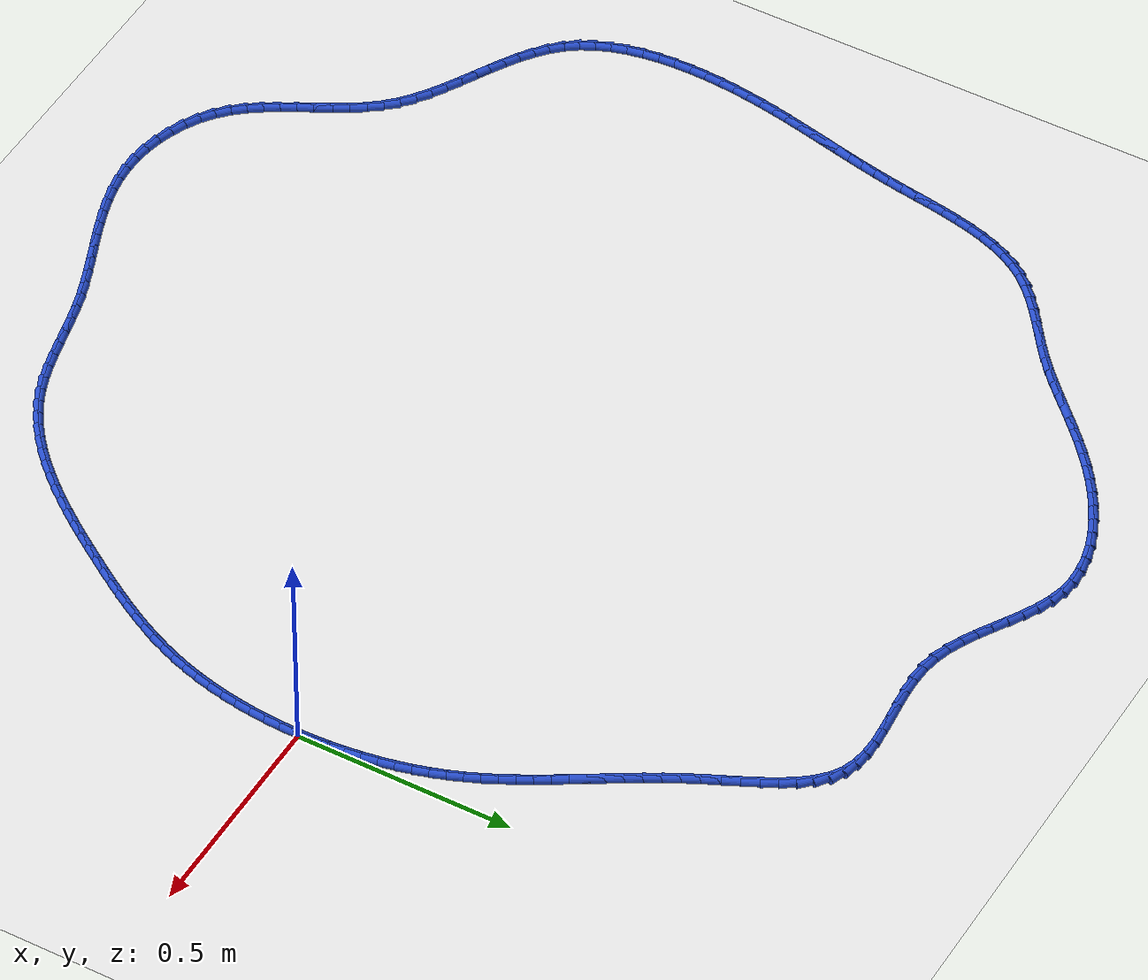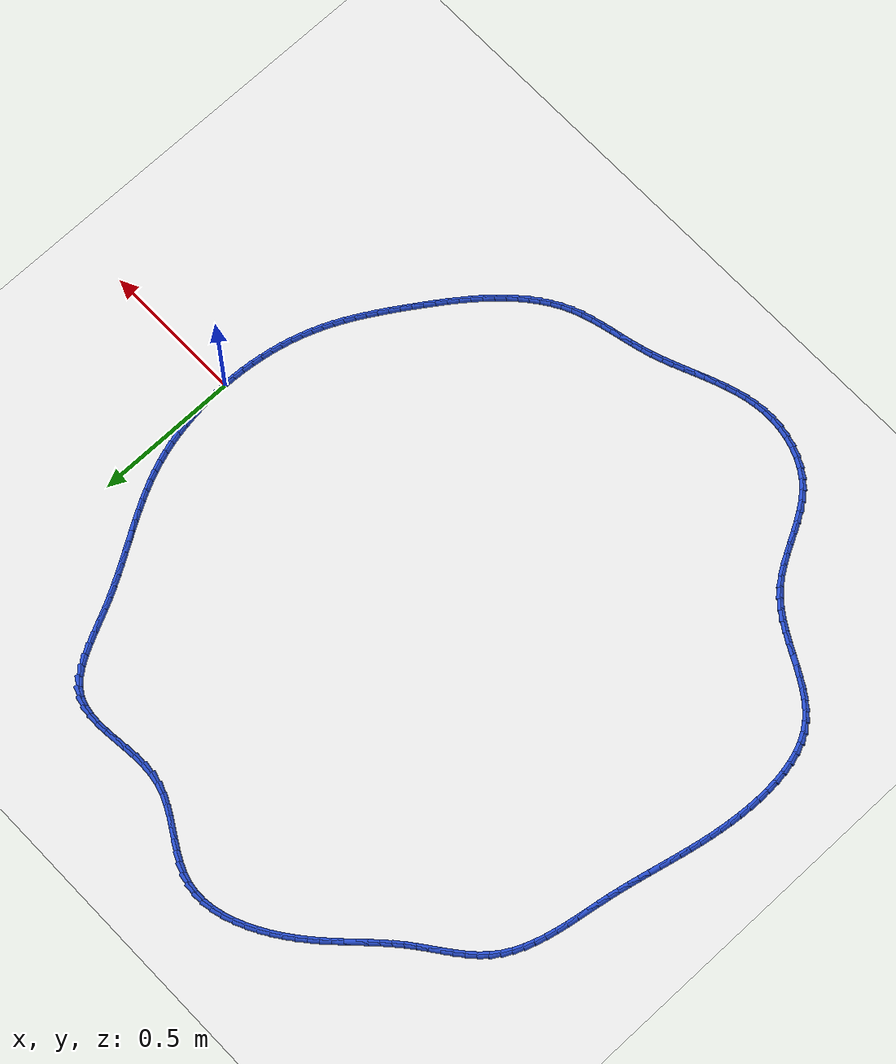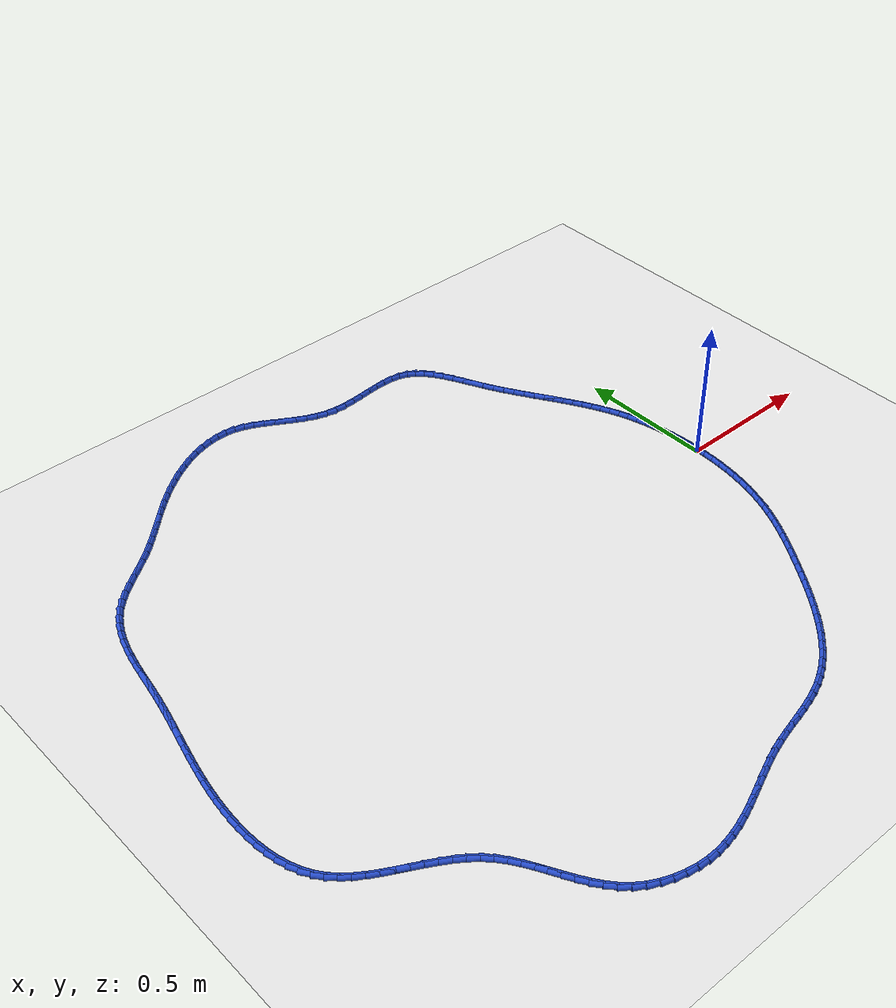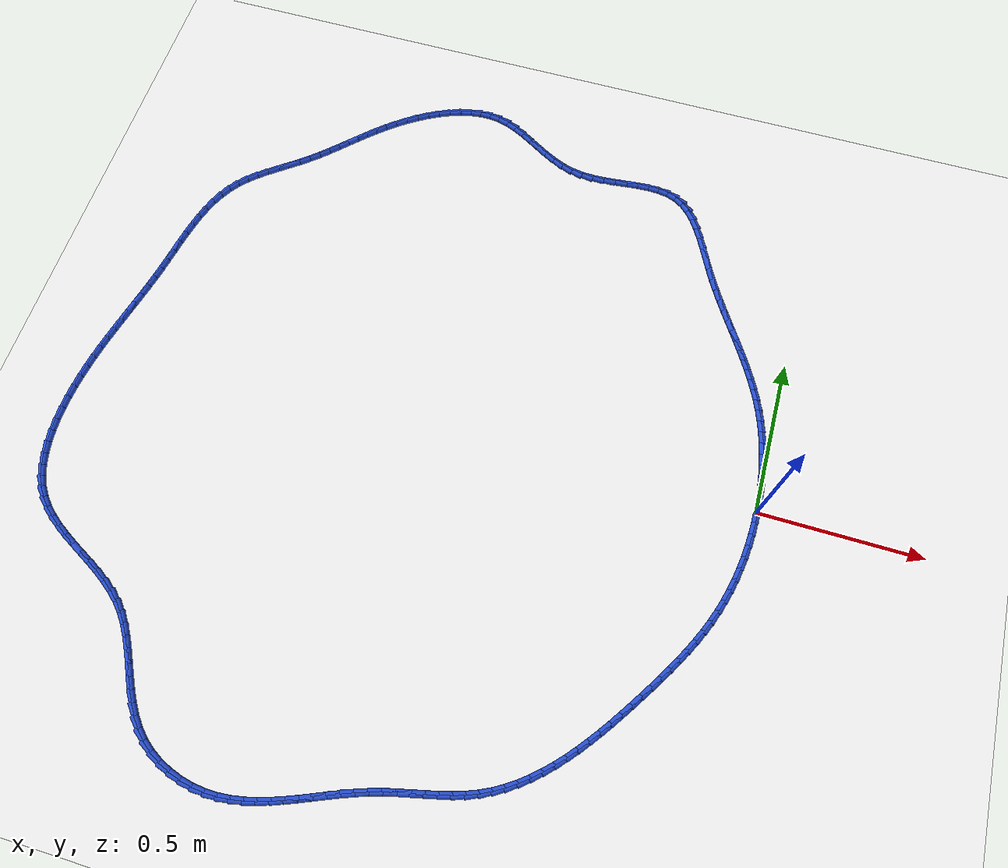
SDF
<sdf version="1.6">
 <world name="default">
  <light name="sun" type="directional">
   <pose>0 0 10 0 -0 0</pose>
   <diffuse>0.8 0.8 0.8 1</diffuse>
   <specular>0.2 0.2 0.2 1</specular>
   <attenuation>
    <range>1000</range>
    <constant>0.9</constant>
    <linear>0.01</linear>
    <quadratic>0.001</quadratic>
   </attenuation>
   <direction>-0.5 0.1 -0.9</direction>
  </light>
  <model name="ground_plane">
   <static>1</static>
   <link name="link">
    <collision name="collision">
     <geometry><plane><normal>0 0 1</normal><size>100 100</size></plane></geometry>
     <surface><friction><ode><mu>100</mu><mu2>50</mu2></ode></friction></surface>
    </collision>
    <visual name="visual">
     <cast_shadows>0</cast_shadows>
     <geometry><plane><normal>0 0 1</normal><size>100 100</size></plane></geometry>
     <material>
      <script><uri>file://media/materials/scripts/gazebo.material</uri><name>Gazebo/WhiteGlow</name></script>
     </material>
    </visual>
   </link>
  </model>
  <gravity>0 0 -9.8</gravity>
  <magnetic_field>6e-06 2.3e-05 -4.2e-05</magnetic_field>
  <atmosphere type="adiabatic"/>
  <physics name="default_physics" default="0" type="ode">
   <max_step_size>0.001</max_step_size>
   <real_time_factor>1</real_time_factor>
   <real_time_update_rate>1000</real_time_update_rate>
  </physics>
  <scene><ambient>0.4 0.4 0.4 1</ambient><background>0.7 0.7 0.7 1</background><shadows>1</shadows></scene>
  <spherical_coordinates>
   <surface_model>EARTH_WGS84</surface_model>
   <latitude_deg>0</latitude_deg>
   <longitude_deg>0</longitude_deg>
   <elevation>0</elevation>
   <heading_deg>0</heading_deg>
  </spherical_coordinates>
  <model name="line">
   <link name="link_0">
    <pose>1.8214596497756474e-17 -2.0816681711721685e-17 0.01 0 1.57 -1.5531008753679438</pose>
    <collision name="collision">
     <geometry><cylinder><radius>0.01</radius><length>0.08</length></cylinder></geometry>
    </collision>
    <visual name="visual">
     <material>
      <script><name>Gazebo/Blue</name><uri>file://media/materials/scripts/gazebo.material</uri></script>
     </material>
     <geometry><cylinder><radius>0.01</radius><length>0.08</length></cylinder></geometry>
    </visual>
   </link>
   <link name="link_1">
    <pose>-0.0006595431757663852 0.03726801411950366 0.01 0 1.57 -1.5183915516718212</pose>
    <collision name="collision">
     <geometry><cylinder><radius>0.01</radius><length>0.08</length></cylinder></geometry>
    </collision>
    <visual name="visual">
     <material>
      <script><name>Gazebo/Blue</name><uri>file://media/materials/scripts/gazebo.material</uri></script>
     </material>
     <geometry><cylinder><radius>0.01</radius><length>0.08</length></cylinder></geometry>
    </visual>
   </link>
   <link name="link_2">
    <pose>-0.0026119037646673057 0.07448929837831636 0.01 0 1.57 -1.4829317528468102</pose>
    <collision name="collision">
     <geometry><cylinder><radius>0.01</radius><length>0.08</length></cylinder></geometry>
    </collision>
    <visual name="visual">
     <material>
      <script><name>Gazebo/Blue</name><uri>file://media/materials/scripts/gazebo.material</uri></script>
     </material>
     <geometry><cylinder><radius>0.01</radius><length>0.08</length></cylinder></geometry>
    </visual>
   </link>
   <link name="link_3">
    <pose>-0.005877130637790065 0.11155565723239855 0.01 0 1.57 -1.4465018681084476</pose>
    <collision name="collision">
     <geometry><cylinder><radius>0.01</radius><length>0.08</length></cylinder></geometry>
    </collision>
    <visual name="visual">
     <material>
      <script><name>Gazebo/Blue</name><uri>file://media/materials/scripts/gazebo.material</uri></script>
     </material>
     <geometry><cylinder><radius>0.01</radius><length>0.08</length></cylinder></geometry>
    </visual>
   </link>
   <link name="link_4">
    <pose>-0.010475272666221972 0.1483588951377105 0.01 0 1.57 -1.408877693254587</pose>
    <collision name="collision">
     <geometry><cylinder><radius>0.01</radius><length>0.08</length></cylinder></geometry>
    </collision>
    <visual name="visual">
     <material>
      <script><name>Gazebo/Blue</name><uri>file://media/materials/scripts/gazebo.material</uri></script>
     </material>
     <geometry><cylinder><radius>0.01</radius><length>0.08</length></cylinder></geometry>
    </visual>
   </link>
   <link name="link_5">
    <pose>-0.016426378721050343 0.18479081655021276 0.01 0 1.57 -1.3698292439418869</pose>
    <collision name="collision">
     <geometry><cylinder><radius>0.01</radius><length>0.08</length></cylinder></geometry>
    </collision>
    <visual name="visual">
     <material>
      <script><name>Gazebo/Blue</name><uri>file://media/materials/scripts/gazebo.material</uri></script>
     </material>
     <geometry><cylinder><radius>0.01</radius><length>0.08</length></cylinder></geometry>
    </visual>
   </link>
   <link name="link_6">
    <pose>-0.023750497673362493 0.22074322592586548 0.01 0 1.57 -1.3291203028907255</pose>
    <collision name="collision">
     <geometry><cylinder><radius>0.01</radius><length>0.08</length></cylinder></geometry>
    </collision>
    <visual name="visual">
     <material>
      <script><name>Gazebo/Blue</name><uri>file://media/materials/scripts/gazebo.material</uri></script>
     </material>
     <geometry><cylinder><radius>0.01</radius><length>0.08</length></cylinder></geometry>
    </visual>
   </link>
   <link name="link_7">
    <pose>-0.032467678394245726 0.2561079277206291 0.01 0 1.57 -1.2865089506136929</pose>
    <collision name="collision">
     <geometry><cylinder><radius>0.01</radius><length>0.08</length></cylinder></geometry>
    </collision>
    <visual name="visual">
     <material>
      <script><name>Gazebo/Blue</name><uri>file://media/materials/scripts/gazebo.material</uri></script>
     </material>
     <geometry><cylinder><radius>0.01</radius><length>0.08</length></cylinder></geometry>
    </visual>
   </link>
   <link name="link_8">
    <pose>-0.04259796975478737 0.29077672639046404 0.01 0 1.57 -1.2417494147548045</pose>
    <collision name="collision">
     <geometry><cylinder><radius>0.01</radius><length>0.08</length></cylinder></geometry>
    </collision>
    <visual name="visual">
     <material>
      <script><name>Gazebo/Blue</name><uri>file://media/materials/scripts/gazebo.material</uri></script>
     </material>
     <geometry><cylinder><radius>0.01</radius><length>0.08</length></cylinder></geometry>
    </visual>
   </link>
   <link name="link_9">
    <pose>-0.054161420626074736 0.32464142639133076 0.01 0 1.57 -1.1957938986238141</pose>
    <collision name="collision">
     <geometry><cylinder><radius>0.01</radius><length>0.08</length></cylinder></geometry>
    </collision>
    <visual name="visual">
     <material>
      <script><name>Gazebo/Blue</name><uri>file://media/materials/scripts/gazebo.material</uri></script>
     </material>
     <geometry><cylinder><radius>0.01</radius><length>0.08</length></cylinder></geometry>
    </visual>
   </link>
   <link name="link_10">
    <pose>-0.06714964277834262 0.35763749528626704 0.01 0 1.57 -1.153555321344448</pose>
    <collision name="collision">
     <geometry><cylinder><radius>0.01</radius><length>0.08</length></cylinder></geometry>
    </collision>
    <visual name="visual">
     <material>
      <script><name>Gazebo/Blue</name><uri>file://media/materials/scripts/gazebo.material</uri></script>
     </material>
     <geometry><cylinder><radius>0.01</radius><length>0.08</length></cylinder></geometry>
    </visual>
   </link>
   <link name="link_11">
    <pose>-0.08143990546992474 0.3898759652771447 0.01 0 1.57 -1.1167319706516843</pose>
    <collision name="collision">
     <geometry><cylinder><radius>0.01</radius><length>0.08</length></cylinder></geometry>
    </collision>
    <visual name="visual">
     <material>
      <script><name>Gazebo/Blue</name><uri>file://media/materials/scripts/gazebo.material</uri></script>
     </material>
     <geometry><cylinder><radius>0.01</radius><length>0.08</length></cylinder></geometry>
    </visual>
   </link>
   <link name="link_12">
    <pose>-0.09688074302912315 0.42151198896802916 0.01 0 1.57 -1.0856952835334408</pose>
    <collision name="collision">
     <geometry><cylinder><radius>0.01</radius><length>0.08</length></cylinder></geometry>
    </collision>
    <visual name="visual">
     <material>
      <script><name>Gazebo/Blue</name><uri>file://media/materials/scripts/gazebo.material</uri></script>
     </material>
     <geometry><cylinder><radius>0.01</radius><length>0.08</length></cylinder></geometry>
    </visual>
   </link>
   <link name="link_13">
    <pose>-0.11332068978409014 0.45270071896321595 0.01 0 1.57 -1.0606653323818236</pose>
    <collision name="collision">
     <geometry><cylinder><radius>0.01</radius><length>0.08</length></cylinder></geometry>
    </collision>
    <visual name="visual">
     <material>
      <script><name>Gazebo/Blue</name><uri>file://media/materials/scripts/gazebo.material</uri></script>
     </material>
     <geometry><cylinder><radius>0.01</radius><length>0.08</length></cylinder></geometry>
    </visual>
   </link>
   <link name="link_14">
    <pose>-0.13060828006297803 0.48359730786700056 0.01 0 1.57 -1.0417359936471429</pose>
    <collision name="collision">
     <geometry><cylinder><radius>0.01</radius><length>0.08</length></cylinder></geometry>
    </collision>
    <visual name="visual">
     <material>
      <script><name>Gazebo/Blue</name><uri>file://media/materials/scripts/gazebo.material</uri></script>
     </material>
     <geometry><cylinder><radius>0.01</radius><length>0.08</length></cylinder></geometry>
    </visual>
   </link>
   <link name="link_15">
    <pose>-0.14859204819393923 0.5143569082836784 0.01 0 1.57 -1.0289011906888796</pose>
    <collision name="collision">
     <geometry><cylinder><radius>0.01</radius><length>0.08</length></cylinder></geometry>
    </collision>
    <visual name="visual">
     <material>
      <script><name>Gazebo/Blue</name><uri>file://media/materials/scripts/gazebo.material</uri></script>
     </material>
     <geometry><cylinder><radius>0.01</radius><length>0.08</length></cylinder></geometry>
    </visual>
   </link>
   <link name="link_16">
    <pose>-0.167120528505126 0.5451346728175449 0.01 0 1.57 -1.0220781069457552</pose>
    <collision name="collision">
     <geometry><cylinder><radius>0.01</radius><length>0.08</length></cylinder></geometry>
    </collision>
    <visual name="visual">
     <material>
      <script><name>Gazebo/Blue</name><uri>file://media/materials/scripts/gazebo.material</uri></script>
     </material>
     <geometry><cylinder><radius>0.01</radius><length>0.08</length></cylinder></geometry>
    </visual>
   </link>
   <link name="link_17">
    <pose>-0.1860422553246907 0.5760857540728955 0.01 0 1.57 -1.0211251269234725</pose>
    <collision name="collision">
     <geometry><cylinder><radius>0.01</radius><length>0.08</length></cylinder></geometry>
    </collision>
    <visual name="visual">
     <material>
      <script><name>Gazebo/Blue</name><uri>file://media/materials/scripts/gazebo.material</uri></script>
     </material>
     <geometry><cylinder><radius>0.01</radius><length>0.08</length></cylinder></geometry>
    </visual>
   </link>
   <link name="link_18">
    <pose>-0.20520576298078566 0.6073653046540255 0.01 0 1.57 -1.0258537774800243</pose>
    <collision name="collision">
     <geometry><cylinder><radius>0.01</radius><length>0.08</length></cylinder></geometry>
    </collision>
    <visual name="visual">
     <material>
      <script><name>Gazebo/Blue</name><uri>file://media/materials/scripts/gazebo.material</uri></script>
     </material>
     <geometry><cylinder><radius>0.01</radius><length>0.08</length></cylinder></geometry>
    </visual>
   </link>
   <link name="link_19">
    <pose>-0.22445958580156314 0.6391284771652304 0.01 0 1.57 -1.0360350032534396</pose>
    <collision name="collision">
     <geometry><cylinder><radius>0.01</radius><length>0.08</length></cylinder></geometry>
    </collision>
    <visual name="visual">
     <material>
      <script><name>Gazebo/Blue</name><uri>file://media/materials/scripts/gazebo.material</uri></script>
     </material>
     <geometry><cylinder><radius>0.01</radius><length>0.08</length></cylinder></geometry>
    </visual>
   </link>
   <link name="link_20">
    <pose>-0.24365225811517563 0.6715304242108057 0.01 0 1.57 -1.0514007854879697</pose>
    <collision name="collision">
     <geometry><cylinder><radius>0.01</radius><length>0.08</length></cylinder></geometry>
    </collision>
    <visual name="visual">
     <material>
      <script><name>Gazebo/Blue</name><uri>file://media/materials/scripts/gazebo.material</uri></script>
     </material>
     <geometry><cylinder><radius>0.01</radius><length>0.08</length></cylinder></geometry>
    </visual>
   </link>
   <link name="link_21">
    <pose>-0.2626323142497753 0.7047262983950466 0.01 0 1.57 -1.0716425218081818</pose>
    <collision name="collision">
     <geometry><cylinder><radius>0.01</radius><length>0.08</length></cylinder></geometry>
    </collision>
    <visual name="visual">
     <material>
      <script><name>Gazebo/Blue</name><uri>file://media/materials/scripts/gazebo.material</uri></script>
     </material>
     <geometry><cylinder><radius>0.01</radius><length>0.08</length></cylinder></geometry>
    </visual>
   </link>
   <link name="link_22">
    <pose>-0.2812482885335147 0.7388712523222489 0.01 0 1.57 -1.096407815746498</pose>
    <collision name="collision">
     <geometry><cylinder><radius>0.01</radius><length>0.08</length></cylinder></geometry>
    </collision>
    <visual name="visual">
     <material>
      <script><name>Gazebo/Blue</name><uri>file://media/materials/scripts/gazebo.material</uri></script>
     </material>
     <geometry><cylinder><radius>0.01</radius><length>0.08</length></cylinder></geometry>
    </visual>
   </link>
   <link name="link_23">
    <pose>-0.29934871539332547 0.7741204384223458 0.01 0 1.57 -1.1206845722338363</pose>
    <collision name="collision">
     <geometry><cylinder><radius>0.01</radius><length>0.08</length></cylinder></geometry>
    </collision>
    <visual name="visual">
     <material>
      <script><name>Gazebo/Blue</name><uri>file://media/materials/scripts/gazebo.material</uri></script>
     </material>
     <geometry><cylinder><radius>0.01</radius><length>0.08</length></cylinder></geometry>
    </visual>
   </link>
   <link name="link_24">
    <pose>-0.3168939900372159 0.8104315565579233 0.01 0 1.57 -1.1269585407032419</pose>
    <collision name="collision">
     <geometry><cylinder><radius>0.01</radius><length>0.08</length></cylinder></geometry>
    </collision>
    <visual name="visual">
     <material>
      <script><name>Gazebo/Blue</name><uri>file://media/materials/scripts/gazebo.material</uri></script>
     </material>
     <geometry><cylinder><radius>0.01</radius><length>0.08</length></cylinder></geometry>
    </visual>
   </link>
   <link name="link_25">
    <pose>-0.3342791364063857 0.8469951158175936 0.01 0 1.57 -1.1112781385612371</pose>
    <collision name="collision">
     <geometry><cylinder><radius>0.01</radius><length>0.08</length></cylinder></geometry>
    </collision>
    <visual name="visual">
     <material>
      <script><name>Gazebo/Blue</name><uri>file://media/materials/scripts/gazebo.material</uri></script>
     </material>
     <geometry><cylinder><radius>0.01</radius><length>0.08</length></cylinder></geometry>
    </visual>
   </link>
   <link name="link_26">
    <pose>-0.35200472325983595 0.8828153214304328 0.01 0 1.57 -1.0719714859968976</pose>
    <collision name="collision">
     <geometry><cylinder><radius>0.01</radius><length>0.08</length></cylinder></geometry>
    </collision>
    <visual name="visual">
     <material>
      <script><name>Gazebo/Blue</name><uri>file://media/materials/scripts/gazebo.material</uri></script>
     </material>
     <geometry><cylinder><radius>0.01</radius><length>0.08</length></cylinder></geometry>
    </visual>
   </link>
   <link name="link_27">
    <pose>-0.3705713193565679 0.9168963786255176 0.01 0 1.57 -1.0049611914783525</pose>
    <collision name="collision">
     <geometry><cylinder><radius>0.01</radius><length>0.08</length></cylinder></geometry>
    </collision>
    <visual name="visual">
     <material>
      <script><name>Gazebo/Blue</name><uri>file://media/materials/scripts/gazebo.material</uri></script>
     </material>
     <geometry><cylinder><radius>0.01</radius><length>0.08</length></cylinder></geometry>
    </visual>
   </link>
   <link name="link_28">
    <pose>-0.39047949345558297 0.9482424926319253 0.01 0 1.57 -0.9036521543529622</pose>
    <collision name="collision">
     <geometry><cylinder><radius>0.01</radius><length>0.08</length></cylinder></geometry>
    </collision>
    <visual name="visual">
     <material>
      <script><name>Gazebo/Blue</name><uri>file://media/materials/scripts/gazebo.material</uri></script>
     </material>
     <geometry><cylinder><radius>0.01</radius><length>0.08</length></cylinder></geometry>
    </visual>
   </link>
   <link name="link_29">
    <pose>-0.41222981431588235 0.975857868678732 0.01 0 1.57 -0.7597727631736094</pose>
    <collision name="collision">
     <geometry><cylinder><radius>0.01</radius><length>0.08</length></cylinder></geometry>
    </collision>
    <visual name="visual">
     <material>
      <script><name>Gazebo/Blue</name><uri>file://media/materials/scripts/gazebo.material</uri></script>
     </material>
     <geometry><cylinder><radius>0.01</radius><length>0.08</length></cylinder></geometry>
    </visual>
   </link>
   <link name="link_30">
    <pose>-0.436322850696467 0.9987467119950144 0.01 0 1.57 -0.5673966069939078</pose>
    <collision name="collision">
     <geometry><cylinder><radius>0.01</radius><length>0.08</length></cylinder></geometry>
    </collision>
    <visual name="visual">
     <material>
      <script><name>Gazebo/Blue</name><uri>file://media/materials/scripts/gazebo.material</uri></script>
     </material>
     <geometry><cylinder><radius>0.01</radius><length>0.08</length></cylinder></geometry>
    </visual>
   </link>
   <link name="link_31">
    <pose>-0.46325915484791785 1.0159132641402708 0.01 0 1.57 -0.3467041414615082</pose>
    <collision name="collision">
     <geometry><cylinder><radius>0.01</radius><length>0.08</length></cylinder></geometry>
    </collision>
    <visual name="visual">
     <material>
      <script><name>Gazebo/Blue</name><uri>file://media/materials/scripts/gazebo.material</uri></script>
     </material>
     <geometry><cylinder><radius>0.01</radius><length>0.08</length></cylinder></geometry>
    </visual>
   </link>
   <link name="link_32">
    <pose>-0.4933473817771319 1.0267840788976763 0.01 0 1.57 -0.16493458311249</pose>
    <collision name="collision">
     <geometry><cylinder><radius>0.01</radius><length>0.08</length></cylinder></geometry>
    </collision>
    <visual name="visual">
     <material>
      <script><name>Gazebo/Blue</name><uri>file://media/materials/scripts/gazebo.material</uri></script>
     </material>
     <geometry><cylinder><radius>0.01</radius><length>0.08</length></cylinder></geometry>
    </visual>
   </link>
   <link name="link_33">
    <pose>-0.5262276851728339 1.0322568946947934 0.01 0 1.57 -0.03674275675983046</pose>
    <collision name="collision">
     <geometry><cylinder><radius>0.01</radius><length>0.08</length></cylinder></geometry>
    </collision>
    <visual name="visual">
     <material>
      <script><name>Gazebo/Blue</name><uri>file://media/materials/scripts/gazebo.material</uri></script>
     </material>
     <geometry><cylinder><radius>0.01</radius><length>0.08</length></cylinder></geometry>
    </visual>
   </link>
   <link name="link_34">
    <pose>-0.5613947386432436 1.0335496109741087 0.01 0 1.57 0.045153391238537684</pose>
    <collision name="collision">
     <geometry><cylinder><radius>0.01</radius><length>0.08</length></cylinder></geometry>
    </collision>
    <visual name="visual">
     <material>
      <script><name>Gazebo/Blue</name><uri>file://media/materials/scripts/gazebo.material</uri></script>
     </material>
     <geometry><cylinder><radius>0.01</radius><length>0.08</length></cylinder></geometry>
    </visual>
   </link>
   <link name="link_35">
    <pose>-0.5983432157965802 1.0318801271781077 0.01 0 1.57 0.08907231843675277</pose>
    <collision name="collision">
     <geometry><cylinder><radius>0.01</radius><length>0.08</length></cylinder></geometry>
    </collision>
    <visual name="visual">
     <material>
      <script><name>Gazebo/Blue</name><uri>file://media/materials/scripts/gazebo.material</uri></script>
     </material>
     <geometry><cylinder><radius>0.01</radius><length>0.08</length></cylinder></geometry>
    </visual>
   </link>
   <link name="link_36">
    <pose>-0.6365677902410642 1.0284663427492764 0.01 0 1.57 0.1007006841445614</pose>
    <collision name="collision">
     <geometry><cylinder><radius>0.01</radius><length>0.08</length></cylinder></geometry>
    </collision>
    <visual name="visual">
     <material>
      <script><name>Gazebo/Blue</name><uri>file://media/materials/scripts/gazebo.material</uri></script>
     </material>
     <geometry><cylinder><radius>0.01</radius><length>0.08</length></cylinder></geometry>
    </visual>
   </link>
   <link name="link_37">
    <pose>-0.6755631355849148 1.024526157130101 0.01 0 1.57 0.08255827627250076</pose>
    <collision name="collision">
     <geometry><cylinder><radius>0.01</radius><length>0.08</length></cylinder></geometry>
    </collision>
    <visual name="visual">
     <material>
      <script><name>Gazebo/Blue</name><uri>file://media/materials/scripts/gazebo.material</uri></script>
     </material>
     <geometry><cylinder><radius>0.01</radius><length>0.08</length></cylinder></geometry>
    </visual>
   </link>
   <link name="link_38">
    <pose>-0.7148239254363519 1.0212774697630673 0.01 0 1.57 0.03430889254589658</pose>
    <collision name="collision">
     <geometry><cylinder><radius>0.01</radius><length>0.08</length></cylinder></geometry>
    </collision>
    <visual name="visual">
     <material>
      <script><name>Gazebo/Blue</name><uri>file://media/materials/scripts/gazebo.material</uri></script>
     </material>
     <geometry><cylinder><radius>0.01</radius><length>0.08</length></cylinder></geometry>
    </visual>
   </link>
   <link name="link_39">
    <pose>-0.7538448334035953 1.0199381800906615 0.01 0 1.57 -0.04667997160673434</pose>
    <collision name="collision">
     <geometry><cylinder><radius>0.01</radius><length>0.08</length></cylinder></geometry>
    </collision>
    <visual name="visual">
     <material>
      <script><name>Gazebo/Blue</name><uri>file://media/materials/scripts/gazebo.material</uri></script>
     </material>
     <geometry><cylinder><radius>0.01</radius><length>0.08</length></cylinder></geometry>
    </visual>
   </link>
   <link name="link_40">
    <pose>-0.7921205330948645 1.0217261875553691 0.01 0 1.57 -0.1639612248776783</pose>
    <collision name="collision">
     <geometry><cylinder><radius>0.01</radius><length>0.08</length></cylinder></geometry>
    </collision>
    <visual name="visual">
     <material>
      <script><name>Gazebo/Blue</name><uri>file://media/materials/scripts/gazebo.material</uri></script>
     </material>
     <geometry><cylinder><radius>0.01</radius><length>0.08</length></cylinder></geometry>
    </visual>
   </link>
   <link name="link_41">
    <pose>-0.8291480905089952 1.027852266231556 0.01 0 1.57 -0.29802096231443126</pose>
    <collision name="collision">
     <geometry><cylinder><radius>0.01</radius><length>0.08</length></cylinder></geometry>
    </collision>
    <visual name="visual">
     <material>
      <script><name>Gazebo/Blue</name><uri>file://media/materials/scripts/gazebo.material</uri></script>
     </material>
     <geometry><cylinder><radius>0.01</radius><length>0.08</length></cylinder></geometry>
    </visual>
   </link>
   <link name="link_42">
    <pose>-0.8646799582709335 1.038766560339869 0.01 0 1.57 -0.4059049006916097</pose>
    <collision name="collision">
     <geometry><cylinder><radius>0.01</radius><length>0.08</length></cylinder></geometry>
    </collision>
    <visual name="visual">
     <material>
      <script><name>Gazebo/Blue</name><uri>file://media/materials/scripts/gazebo.material</uri></script>
     </material>
     <geometry><cylinder><radius>0.01</radius><length>0.08</length></cylinder></geometry>
    </visual>
   </link>
   <link name="link_43">
    <pose>-0.8989472330487357 1.0534936463097262 0.01 0 1.57 -0.4818508658149781</pose>
    <collision name="collision">
     <geometry><cylinder><radius>0.01</radius><length>0.08</length></cylinder></geometry>
    </collision>
    <visual name="visual">
     <material>
      <script><name>Gazebo/Blue</name><uri>file://media/materials/scripts/gazebo.material</uri></script>
     </material>
     <geometry><cylinder><radius>0.01</radius><length>0.08</length></cylinder></geometry>
    </visual>
   </link>
   <link name="link_44">
    <pose>-0.9322336575721422 1.070901302359117 0.01 0 1.57 -0.5268273854434528</pose>
    <collision name="collision">
     <geometry><cylinder><radius>0.01</radius><length>0.08</length></cylinder></geometry>
    </collision>
    <visual name="visual">
     <material>
      <script><name>Gazebo/Blue</name><uri>file://media/materials/scripts/gazebo.material</uri></script>
     </material>
     <geometry><cylinder><radius>0.01</radius><length>0.08</length></cylinder></geometry>
    </visual>
   </link>
   <link name="link_45">
    <pose>-0.9648229745708924 1.0898573067060315 0.01 0 1.57 -0.5419391499948902</pose>
    <collision name="collision">
     <geometry><cylinder><radius>0.01</radius><length>0.08</length></cylinder></geometry>
    </collision>
    <visual name="visual">
     <material>
      <script><name>Gazebo/Blue</name><uri>file://media/materials/scripts/gazebo.material</uri></script>
     </material>
     <geometry><cylinder><radius>0.01</radius><length>0.08</length></cylinder></geometry>
    </visual>
   </link>
   <link name="link_46">
    <pose>-0.9969989267747262 1.1092294375684584 0.01 0 1.57 -0.5271972567870595</pose>
    <collision name="collision">
     <geometry><cylinder><radius>0.01</radius><length>0.08</length></cylinder></geometry>
    </collision>
    <visual name="visual">
     <material>
      <script><name>Gazebo/Blue</name><uri>file://media/materials/scripts/gazebo.material</uri></script>
     </material>
     <geometry><cylinder><radius>0.01</radius><length>0.08</length></cylinder></geometry>
    </visual>
   </link>
   <link name="link_47">
    <pose>-1.029045256913383 1.1278854731643875 0.01 0 1.57 -0.4810699358292078</pose>
    <collision name="collision">
     <geometry><cylinder><radius>0.01</radius><length>0.08</length></cylinder></geometry>
    </collision>
    <visual name="visual">
     <material>
      <script><name>Gazebo/Blue</name><uri>file://media/materials/scripts/gazebo.material</uri></script>
     </material>
     <geometry><cylinder><radius>0.01</radius><length>0.08</length></cylinder></geometry>
    </visual>
   </link>
   <link name="link_48">
    <pose>-1.0612457077166029 1.1446931917118084 0.01 0 1.57 -0.4007255364006845</pose>
    <collision name="collision">
     <geometry><cylinder><radius>0.01</radius><length>0.08</length></cylinder></geometry>
    </collision>
    <visual name="visual">
     <material>
      <script><name>Gazebo/Blue</name><uri>file://media/materials/scripts/gazebo.material</uri></script>
     </material>
     <geometry><cylinder><radius>0.01</radius><length>0.08</length></cylinder></geometry>
    </visual>
   </link>
   <link name="link_49">
    <pose>-1.0938840219141255 1.1585203714287102 0.01 0 1.57 -0.2833642600836688</pose>
    <collision name="collision">
     <geometry><cylinder><radius>0.01</radius><length>0.08</length></cylinder></geometry>
    </collision>
    <visual name="visual">
     <material>
      <script><name>Gazebo/Blue</name><uri>file://media/materials/scripts/gazebo.material</uri></script>
     </material>
     <geometry><cylinder><radius>0.01</radius><length>0.08</length></cylinder></geometry>
    </visual>
   </link>
   <link name="link_50">
    <pose>-1.1272439422356908 1.168234790533083 0.01 0 1.57 -0.1348694033147934</pose>
    <collision name="collision">
     <geometry><cylinder><radius>0.01</radius><length>0.08</length></cylinder></geometry>
    </collision>
    <visual name="visual">
     <material>
      <script><name>Gazebo/Blue</name><uri>file://media/materials/scripts/gazebo.material</uri></script>
     </material>
     <geometry><cylinder><radius>0.01</radius><length>0.08</length></cylinder></geometry>
    </visual>
   </link>
   <link name="link_51">
    <pose>-1.1615433456143536 1.172888984431039 0.01 0 1.57 0.008827553071048792</pose>
    <collision name="collision">
     <geometry><cylinder><radius>0.01</radius><length>0.08</length></cylinder></geometry>
    </collision>
    <visual name="visual">
     <material>
      <script><name>Gazebo/Blue</name><uri>file://media/materials/scripts/gazebo.material</uri></script>
     </material>
     <geometry><cylinder><radius>0.01</radius><length>0.08</length></cylinder></geometry>
    </visual>
   </link>
   <link name="link_52">
    <pose>-1.196628003571907 1.172579264705856 0.01 0 1.57 0.13438621315433963</pose>
    <collision name="collision">
     <geometry><cylinder><radius>0.01</radius><length>0.08</length></cylinder></geometry>
    </collision>
    <visual name="visual">
     <material>
      <script><name>Gazebo/Blue</name><uri>file://media/materials/scripts/gazebo.material</uri></script>
     </material>
     <geometry><cylinder><radius>0.01</radius><length>0.08</length></cylinder></geometry>
    </visual>
   </link>
   <link name="link_53">
    <pose>-1.2322131477729057 1.1677681144315575 0.01 0 1.57 0.2423354071631003</pose>
    <collision name="collision">
     <geometry><cylinder><radius>0.01</radius><length>0.08</length></cylinder></geometry>
    </collision>
    <visual name="visual">
     <material>
      <script><name>Gazebo/Blue</name><uri>file://media/materials/scripts/gazebo.material</uri></script>
     </material>
     <geometry><cylinder><radius>0.01</radius><length>0.08</length></cylinder></geometry>
    </visual>
   </link>
   <link name="link_54">
    <pose>-1.268013868620136 1.1589184129292132 0.01 0 1.57 0.33466354929036196</pose>
    <collision name="collision">
     <geometry><cylinder><radius>0.01</radius><length>0.08</length></cylinder></geometry>
    </collision>
    <visual name="visual">
     <material>
      <script><name>Gazebo/Blue</name><uri>file://media/materials/scripts/gazebo.material</uri></script>
     </material>
     <geometry><cylinder><radius>0.01</radius><length>0.08</length></cylinder></geometry>
    </visual>
   </link>
   <link name="link_55">
    <pose>-1.3037452565163834 1.146493039519893 0.01 0 1.57 0.4138488465739483</pose>
    <collision name="collision">
     <geometry><cylinder><radius>0.01</radius><length>0.08</length></cylinder></geometry>
    </collision>
    <visual name="visual">
     <material>
      <script><name>Gazebo/Blue</name><uri>file://media/materials/scripts/gazebo.material</uri></script>
     </material>
     <geometry><cylinder><radius>0.01</radius><length>0.08</length></cylinder></geometry>
    </visual>
   </link>
   <link name="link_56">
    <pose>-1.3391224018644323 1.1309548735246664 0.01 0 1.57 0.48233228513844634</pose>
    <collision name="collision">
     <geometry><cylinder><radius>0.01</radius><length>0.08</length></cylinder></geometry>
    </collision>
    <visual name="visual">
     <material>
      <script><name>Gazebo/Blue</name><uri>file://media/materials/scripts/gazebo.material</uri></script>
     </material>
     <geometry><cylinder><radius>0.01</radius><length>0.08</length></cylinder></geometry>
    </visual>
   </link>
   <link name="link_57">
    <pose>-1.3738603950670685 1.1127667942646033 0.01 0 1.57 0.5423038640991938</pose>
    <collision name="collision">
     <geometry><cylinder><radius>0.01</radius><length>0.08</length></cylinder></geometry>
    </collision>
    <visual name="visual">
     <material>
      <script><name>Gazebo/Blue</name><uri>file://media/materials/scripts/gazebo.material</uri></script>
     </material>
     <geometry><cylinder><radius>0.01</radius><length>0.08</length></cylinder></geometry>
    </visual>
   </link>
   <link name="link_58">
    <pose>-1.4076743265270772 1.0923916810607734 0.01 0 1.57 0.5956628795325257</pose>
    <collision name="collision">
     <geometry><cylinder><radius>0.01</radius><length>0.08</length></cylinder></geometry>
    </collision>
    <visual name="visual">
     <material>
      <script><name>Gazebo/Blue</name><uri>file://media/materials/scripts/gazebo.material</uri></script>
     </material>
     <geometry><cylinder><radius>0.01</radius><length>0.08</length></cylinder></geometry>
    </visual>
   </link>
   <link name="link_59">
    <pose>-1.4402792866472434 1.0702924132342468 0.01 0 1.57 0.6440611109630304</pose>
    <collision name="collision">
     <geometry><cylinder><radius>0.01</radius><length>0.08</length></cylinder></geometry>
    </collision>
    <visual name="visual">
     <material>
      <script><name>Gazebo/Blue</name><uri>file://media/materials/scripts/gazebo.material</uri></script>
     </material>
     <geometry><cylinder><radius>0.01</radius><length>0.08</length></cylinder></geometry>
    </visual>
   </link>
   <link name="link_60">
    <pose>-1.4713903658303535 1.046931870106093 0.01 0 1.57 0.6882938133641108</pose>
    <collision name="collision">
     <geometry><cylinder><radius>0.01</radius><length>0.08</length></cylinder></geometry>
    </collision>
    <visual name="visual">
     <material>
      <script><name>Gazebo/Blue</name><uri>file://media/materials/scripts/gazebo.material</uri></script>
     </material>
     <geometry><cylinder><radius>0.01</radius><length>0.08</length></cylinder></geometry>
    </visual>
   </link>
   <link name="link_61">
    <pose>-1.5008133917872155 1.0227322630536195 0.01 0 1.57 0.725675912529105</pose>
    <collision name="collision">
     <geometry><cylinder><radius>0.01</radius><length>0.08</length></cylinder></geometry>
    </collision>
    <visual name="visual">
     <material>
      <script><name>Gazebo/Blue</name><uri>file://media/materials/scripts/gazebo.material</uri></script>
     </material>
     <geometry><cylinder><radius>0.01</radius><length>0.08</length></cylinder></geometry>
    </visual>
   </link>
   <link name="link_62">
    <pose>-1.5287718862780761 0.9979285953642972 0.01 0 1.57 0.7544646948901811</pose>
    <collision name="collision">
     <geometry><cylinder><radius>0.01</radius><length>0.08</length></cylinder></geometry>
    </collision>
    <visual name="visual">
     <material>
      <script><name>Gazebo/Blue</name><uri>file://media/materials/scripts/gazebo.material</uri></script>
     </material>
     <geometry><cylinder><radius>0.01</radius><length>0.08</length></cylinder></geometry>
    </visual>
   </link>
   <link name="link_63">
    <pose>-1.5556094841788022 0.972702036312472 0.01 0 1.57 0.7739087278106418</pose>
    <collision name="collision">
     <geometry><cylinder><radius>0.01</radius><length>0.08</length></cylinder></geometry>
    </collision>
    <visual name="visual">
     <material>
      <script><name>Gazebo/Blue</name><uri>file://media/materials/scripts/gazebo.material</uri></script>
     </material>
     <geometry><cylinder><radius>0.01</radius><length>0.08</length></cylinder></geometry>
    </visual>
   </link>
   <link name="link_64">
    <pose>-1.5816698310824684 0.9472337503690967 0.01 0 1.57 0.7834845305671589</pose>
    <collision name="collision">
     <geometry><cylinder><radius>0.01</radius><length>0.08</length></cylinder></geometry>
    </collision>
    <visual name="visual">
     <material>
      <script><name>Gazebo/Blue</name><uri>file://media/materials/scripts/gazebo.material</uri></script>
     </material>
     <geometry><cylinder><radius>0.01</radius><length>0.08</length></cylinder></geometry>
    </visual>
   </link>
   <link name="link_65">
    <pose>-1.6072965725821504 0.9217049020051252 0.01 0 1.57 0.7828751477575939</pose>
    <collision name="collision">
     <geometry><cylinder><radius>0.01</radius><length>0.08</length></cylinder></geometry>
    </collision>
    <visual name="visual">
     <material>
      <script><name>Gazebo/Blue</name><uri>file://media/materials/scripts/gazebo.material</uri></script>
     </material>
     <geometry><cylinder><radius>0.01</radius><length>0.08</length></cylinder></geometry>
    </visual>
   </link>
   <link name="link_66">
    <pose>-1.6328333542709224 0.8962966556915115 0.01 0 1.57 0.7719602944434932</pose>
    <collision name="collision">
     <geometry><cylinder><radius>0.01</radius><length>0.08</length></cylinder></geometry>
    </collision>
    <visual name="visual">
     <material>
      <script><name>Gazebo/Blue</name><uri>file://media/materials/scripts/gazebo.material</uri></script>
     </material>
     <geometry><cylinder><radius>0.01</radius><length>0.08</length></cylinder></geometry>
    </visual>
   </link>
   <link name="link_67">
    <pose>-1.6586238217418603 0.8711901758992088 0.01 0 1.57 0.7508265005349857</pose>
    <collision name="collision">
     <geometry><cylinder><radius>0.01</radius><length>0.08</length></cylinder></geometry>
    </collision>
    <visual name="visual">
     <material>
      <script><name>Gazebo/Blue</name><uri>file://media/materials/scripts/gazebo.material</uri></script>
     </material>
     <geometry><cylinder><radius>0.01</radius><length>0.08</length></cylinder></geometry>
    </visual>
   </link>
   <link name="link_68">
    <pose>-1.6850116205880386 0.8465666270991707 0.01 0 1.57 0.7197985498542236</pose>
    <collision name="collision">
     <geometry><cylinder><radius>0.01</radius><length>0.08</length></cylinder></geometry>
    </collision>
    <visual name="visual">
     <material>
      <script><name>Gazebo/Blue</name><uri>file://media/materials/scripts/gazebo.material</uri></script>
     </material>
     <geometry><cylinder><radius>0.01</radius><length>0.08</length></cylinder></geometry>
    </visual>
   </link>
   <link name="link_69">
    <pose>-1.7123403964025323 0.8226071737623512 0.01 0 1.57 0.6804805687634148</pose>
    <collision name="collision">
     <geometry><cylinder><radius>0.01</radius><length>0.08</length></cylinder></geometry>
    </collision>
    <visual name="visual">
     <material>
      <script><name>Gazebo/Blue</name><uri>file://media/materials/scripts/gazebo.material</uri></script>
     </material>
     <geometry><cylinder><radius>0.01</radius><length>0.08</length></cylinder></geometry>
    </visual>
   </link>
   <link name="link_70">
    <pose>-1.7409207975994136 0.7994725818736622 0.01 0 1.57 0.6499449687900314</pose>
    <collision name="collision">
     <geometry><cylinder><radius>0.01</radius><length>0.08</length></cylinder></geometry>
    </collision>
    <visual name="visual">
     <material>
      <script><name>Gazebo/Blue</name><uri>file://media/materials/scripts/gazebo.material</uri></script>
     </material>
     <geometry><cylinder><radius>0.01</radius><length>0.08</length></cylinder></geometry>
    </visual>
   </link>
   <link name="link_71">
    <pose>-1.7705098856753032 0.7769813961933696 0.01 0 1.57 0.6411658764219705</pose>
    <collision name="collision">
     <geometry><cylinder><radius>0.01</radius><length>0.08</length></cylinder></geometry>
    </collision>
    <visual name="visual">
     <material>
      <script><name>Gazebo/Blue</name><uri>file://media/materials/scripts/gazebo.material</uri></script>
     </material>
     <geometry><cylinder><radius>0.01</radius><length>0.08</length></cylinder></geometry>
    </visual>
   </link>
   <link name="link_72">
    <pose>-1.8004057217242546 0.7546684125799343 0.01 0 1.57 0.6541261754685944</pose>
    <collision name="collision">
     <geometry><cylinder><radius>0.01</radius><length>0.08</length></cylinder></geometry>
    </collision>
    <visual name="visual">
     <material>
      <script><name>Gazebo/Blue</name><uri>file://media/materials/scripts/gazebo.material</uri></script>
     </material>
     <geometry><cylinder><radius>0.01</radius><length>0.08</length></cylinder></geometry>
    </visual>
   </link>
   <link name="link_73">
    <pose>-1.8298924953954614 0.7320598517201561 0.01 0 1.57 0.6893666464556728</pose>
    <collision name="collision">
     <geometry><cylinder><radius>0.01</radius><length>0.08</length></cylinder></geometry>
    </collision>
    <visual name="visual">
     <material>
      <script><name>Gazebo/Blue</name><uri>file://media/materials/scripts/gazebo.material</uri></script>
     </material>
     <geometry><cylinder><radius>0.01</radius><length>0.08</length></cylinder></geometry>
    </visual>
   </link>
   <link name="link_74">
    <pose>-1.8582543963381193 0.7086819343008336 0.01 0 1.57 0.7482607643806226</pose>
    <collision name="collision">
     <geometry><cylinder><radius>0.01</radius><length>0.08</length></cylinder></geometry>
    </collision>
    <visual name="visual">
     <material>
      <script><name>Gazebo/Blue</name><uri>file://media/materials/scripts/gazebo.material</uri></script>
     </material>
     <geometry><cylinder><radius>0.01</radius><length>0.08</length></cylinder></geometry>
    </visual>
   </link>
   <link name="link_75">
    <pose>-1.884775614201423 0.6840608810087662 0.01 0 1.57 0.8325424692199745</pose>
    <collision name="collision">
     <geometry><cylinder><radius>0.01</radius><length>0.08</length></cylinder></geometry>
    </collision>
    <visual name="visual">
     <material>
      <script><name>Gazebo/Blue</name><uri>file://media/materials/scripts/gazebo.material</uri></script>
     </material>
     <geometry><cylinder><radius>0.01</radius><length>0.08</length></cylinder></geometry>
    </visual>
   </link>
   <link name="link_76">
    <pose>-1.9087403386345663 0.6577229125307534 0.01 0 1.57 0.9403603623094907</pose>
    <collision name="collision">
     <geometry><cylinder><radius>0.01</radius><length>0.08</length></cylinder></geometry>
    </collision>
    <visual name="visual">
     <material>
      <script><name>Gazebo/Blue</name><uri>file://media/materials/scripts/gazebo.material</uri></script>
     </material>
     <geometry><cylinder><radius>0.01</radius><length>0.08</length></cylinder></geometry>
    </visual>
   </link>
   <link name="link_77">
    <pose>-1.9295178760421683 0.6292520563337846 0.01 0 1.57 1.0472479316627132</pose>
    <collision name="collision">
     <geometry><cylinder><radius>0.01</radius><length>0.08</length></cylinder></geometry>
    </collision>
    <visual name="visual">
     <material>
      <script><name>Gazebo/Blue</name><uri>file://media/materials/scripts/gazebo.material</uri></script>
     </material>
     <geometry><cylinder><radius>0.01</radius><length>0.08</length></cylinder></geometry>
    </visual>
   </link>
   <link name="link_78">
    <pose>-1.9471581796278907 0.5986945990452689 0.01 0 1.57 1.1400008952900078</pose>
    <collision name="collision">
     <geometry><cylinder><radius>0.01</radius><length>0.08</length></cylinder></geometry>
    </collision>
    <visual name="visual">
     <material>
      <script><name>Gazebo/Blue</name><uri>file://media/materials/scripts/gazebo.material</uri></script>
     </material>
     <geometry><cylinder><radius>0.01</radius><length>0.08</length></cylinder></geometry>
    </visual>
   </link>
   <link name="link_79">
    <pose>-1.9620376920560596 0.5663185615961986 0.01 0 1.57 1.2178457590242198</pose>
    <collision name="collision">
     <geometry><cylinder><radius>0.01</radius><length>0.08</length></cylinder></geometry>
    </collision>
    <visual name="visual">
     <material>
      <script><name>Gazebo/Blue</name><uri>file://media/materials/scripts/gazebo.material</uri></script>
     </material>
     <geometry><cylinder><radius>0.01</radius><length>0.08</length></cylinder></geometry>
    </visual>
   </link>
   <link name="link_80">
    <pose>-1.9745349150667229 0.5323933633324518 0.01 0 1.57 1.2811137499216871</pose>
    <collision name="collision">
     <geometry><cylinder><radius>0.01</radius><length>0.08</length></cylinder></geometry>
    </collision>
    <visual name="visual">
     <material>
      <script><name>Gazebo/Blue</name><uri>file://media/materials/scripts/gazebo.material</uri></script>
     </material>
     <geometry><cylinder><radius>0.01</radius><length>0.08</length></cylinder></geometry>
    </visual>
   </link>
   <link name="link_81">
    <pose>-1.9850283503999318 0.49718842359990556 0.01 0 1.57 1.3306486164743747</pose>
    <collision name="collision">
     <geometry><cylinder><radius>0.01</radius><length>0.08</length></cylinder></geometry>
    </collision>
    <visual name="visual">
     <material>
      <script><name>Gazebo/Blue</name><uri>file://media/materials/scripts/gazebo.material</uri></script>
     </material>
     <geometry><cylinder><radius>0.01</radius><length>0.08</length></cylinder></geometry>
    </visual>
   </link>
   <link name="link_82">
    <pose>-1.9938964997957358 0.46097316174443836 0.01 0 1.57 1.3674203378683245</pose>
    <collision name="collision">
     <geometry><cylinder><radius>0.01</radius><length>0.08</length></cylinder></geometry>
    </collision>
    <visual name="visual">
     <material>
      <script><name>Gazebo/Blue</name><uri>file://media/materials/scripts/gazebo.material</uri></script>
     </material>
     <geometry><cylinder><radius>0.01</radius><length>0.08</length></cylinder></geometry>
    </visual>
   </link>
   <link name="link_83">
    <pose>-2.001517864994184 0.4240169971119282 0.01 0 1.57 1.392286598869336</pose>
    <collision name="collision">
     <geometry><cylinder><radius>0.01</radius><length>0.08</length></cylinder></geometry>
    </collision>
    <visual name="visual">
     <material>
      <script><name>Gazebo/Blue</name><uri>file://media/materials/scripts/gazebo.material</uri></script>
     </material>
     <geometry><cylinder><radius>0.01</radius><length>0.08</length></cylinder></geometry>
    </visual>
   </link>
   <link name="link_84">
    <pose>-2.008270947735328 0.38658934904825243 0.01 0 1.57 1.4058626970710961</pose>
    <collision name="collision">
     <geometry><cylinder><radius>0.01</radius><length>0.08</length></cylinder></geometry>
    </collision>
    <visual name="visual">
     <material>
      <script><name>Gazebo/Blue</name><uri>file://media/materials/scripts/gazebo.material</uri></script>
     </material>
     <geometry><cylinder><radius>0.01</radius><length>0.08</length></cylinder></geometry>
    </visual>
   </link>
   <link name="link_85">
    <pose>-2.0145342497592167 0.34895963689928927 0.01 0 1.57 1.408456044278473</pose>
    <collision name="collision">
     <geometry><cylinder><radius>0.01</radius><length>0.08</length></cylinder></geometry>
    </collision>
    <visual name="visual">
     <material>
      <script><name>Gazebo/Blue</name><uri>file://media/materials/scripts/gazebo.material</uri></script>
     </material>
     <geometry><cylinder><radius>0.01</radius><length>0.08</length></cylinder></geometry>
    </visual>
   </link>
   <link name="link_86">
    <pose>-2.0206862728058987 0.3113972800109169 0.01 0 1.57 1.400033932852301</pose>
    <collision name="collision">
     <geometry><cylinder><radius>0.01</radius><length>0.08</length></cylinder></geometry>
    </collision>
    <visual name="visual">
     <material>
      <script><name>Gazebo/Blue</name><uri>file://media/materials/scripts/gazebo.material</uri></script>
     </material>
     <geometry><cylinder><radius>0.01</radius><length>0.08</length></cylinder></geometry>
    </visual>
   </link>
   <link name="link_87">
    <pose>-2.027105518615425 0.2741716977290123 0.01 0 1.57 1.3825338629292288</pose>
    <collision name="collision">
     <geometry><cylinder><radius>0.01</radius><length>0.08</length></cylinder></geometry>
    </collision>
    <visual name="visual">
     <material>
      <script><name>Gazebo/Blue</name><uri>file://media/materials/scripts/gazebo.material</uri></script>
     </material>
     <geometry><cylinder><radius>0.01</radius><length>0.08</length></cylinder></geometry>
    </visual>
   </link>
   <link name="link_88">
    <pose>-2.0340927615261264 0.23749684491850792 0.01 0 1.57 1.3660504790088808</pose>
    <collision name="collision">
     <geometry><cylinder><radius>0.01</radius><length>0.08</length></cylinder></geometry>
    </collision>
    <visual name="visual">
     <material>
      <script><name>Gazebo/Blue</name><uri>file://media/materials/scripts/gazebo.material</uri></script>
     </material>
     <geometry><cylinder><radius>0.01</radius><length>0.08</length></cylinder></geometry>
    </visual>
   </link>
   <link name="link_89">
    <pose>-2.0416012135900243 0.2013386640139712 0.01 0 1.57 1.3536618402424256</pose>
    <collision name="collision">
     <geometry><cylinder><radius>0.01</radius><length>0.08</length></cylinder></geometry>
    </collision>
    <visual name="visual">
     <material>
      <script><name>Gazebo/Blue</name><uri>file://media/materials/scripts/gazebo.material</uri></script>
     </material>
     <geometry><cylinder><radius>0.01</radius><length>0.08</length></cylinder></geometry>
    </visual>
   </link>
   <link name="link_90">
    <pose>-2.0494869780217764 0.16559380282361508 0.01 0 1.57 1.3455549843047392</pose>
    <collision name="collision">
     <geometry><cylinder><radius>0.01</radius><length>0.08</length></cylinder></geometry>
    </collision>
    <visual name="visual">
     <material>
      <script><name>Gazebo/Blue</name><uri>file://media/materials/scripts/gazebo.material</uri></script>
     </material>
     <geometry><cylinder><radius>0.01</radius><length>0.08</length></cylinder></geometry>
    </visual>
   </link>
   <link name="link_91">
    <pose>-2.0576061535836447 0.13015890597852434 0.01 0 1.57 1.3418672281104156</pose>
    <collision name="collision">
     <geometry><cylinder><radius>0.01</radius><length>0.08</length></cylinder></geometry>
    </collision>
    <visual name="visual">
     <material>
      <script><name>Gazebo/Blue</name><uri>file://media/materials/scripts/gazebo.material</uri></script>
     </material>
     <geometry><cylinder><radius>0.01</radius><length>0.08</length></cylinder></geometry>
    </visual>
   </link>
   <link name="link_92">
    <pose>-2.0658148390378916 0.09493061810978483 0.01 0 1.57 1.3426864507366176</pose>
    <collision name="collision">
     <geometry><cylinder><radius>0.01</radius><length>0.08</length></cylinder></geometry>
    </collision>
    <visual name="visual">
     <material>
      <script><name>Gazebo/Blue</name><uri>file://media/materials/scripts/gazebo.material</uri></script>
     </material>
     <geometry><cylinder><radius>0.01</radius><length>0.08</length></cylinder></geometry>
    </visual>
   </link>
   <link name="link_93">
    <pose>-2.0739691331467762 0.05980558384848233 0.01 0 1.57 1.348050337753554</pose>
    <collision name="collision">
     <geometry><cylinder><radius>0.01</radius><length>0.08</length></cylinder></geometry>
    </collision>
    <visual name="visual">
     <material>
      <script><name>Gazebo/Blue</name><uri>file://media/materials/scripts/gazebo.material</uri></script>
     </material>
     <geometry><cylinder><radius>0.01</radius><length>0.08</length></cylinder></geometry>
    </visual>
   </link>
   <link name="link_94">
    <pose>-2.081925134672563 0.024680447825701717 0.01 0 1.57 1.3579443616122902</pose>
    <collision name="collision">
     <geometry><cylinder><radius>0.01</radius><length>0.08</length></cylinder></geometry>
    </collision>
    <visual name="visual">
     <material>
      <script><name>Gazebo/Blue</name><uri>file://media/materials/scripts/gazebo.material</uri></script>
     </material>
     <geometry><cylinder><radius>0.01</radius><length>0.08</length></cylinder></geometry>
    </visual>
   </link>
   <link name="link_95">
    <pose>-2.0895389423775126 -0.010548145327471177 0.01 0 1.57 1.3722984757282812</pose>
    <collision name="collision">
     <geometry><cylinder><radius>0.01</radius><length>0.08</length></cylinder></geometry>
    </collision>
    <visual name="visual">
     <material>
      <script><name>Gazebo/Blue</name><uri>file://media/materials/scripts/gazebo.material</uri></script>
     </material>
     <geometry><cylinder><radius>0.01</radius><length>0.08</length></cylinder></geometry>
    </visual>
   </link>
   <link name="link_96">
    <pose>-2.096666655023886 -0.04598355097995082 0.01 0 1.57 1.3909828745682344</pose>
    <collision name="collision">
     <geometry><cylinder><radius>0.01</radius><length>0.08</length></cylinder></geometry>
    </collision>
    <visual name="visual">
     <material>
      <script><name>Gazebo/Blue</name><uri>file://media/materials/scripts/gazebo.material</uri></script>
     </material>
     <geometry><cylinder><radius>0.01</radius><length>0.08</length></cylinder></geometry>
    </visual>
   </link>
   <link name="link_97">
    <pose>-2.103164371373946 -0.08172912450065178 0.01 0 1.57 1.4138035531262156</pose>
    <collision name="collision">
     <geometry><cylinder><radius>0.01</radius><length>0.08</length></cylinder></geometry>
    </collision>
    <visual name="visual">
     <material>
      <script><name>Gazebo/Blue</name><uri>file://media/materials/scripts/gazebo.material</uri></script>
     </material>
     <geometry><cylinder><radius>0.01</radius><length>0.08</length></cylinder></geometry>
    </visual>
   </link>
   <link name="link_98">
    <pose>-2.108888190189954 -0.11788822125848772 0.01 0 1.57 1.4404987367272715</pose>
    <collision name="collision">
     <geometry><cylinder><radius>0.01</radius><length>0.08</length></cylinder></geometry>
    </collision>
    <visual name="visual">
     <material>
      <script><name>Gazebo/Blue</name><uri>file://media/materials/scripts/gazebo.material</uri></script>
     </material>
     <geometry><cylinder><radius>0.01</radius><length>0.08</length></cylinder></geometry>
    </visual>
   </link>
   <link name="link_99">
    <pose>-2.1136942102341703 -0.15456419662237467 0.01 0 1.57 1.4707374738841688</pose>
    <collision name="collision">
     <geometry><cylinder><radius>0.01</radius><length>0.08</length></cylinder></geometry>
    </collision>
    <visual name="visual">
     <material>
      <script><name>Gazebo/Blue</name><uri>file://media/materials/scripts/gazebo.material</uri></script>
     </material>
     <geometry><cylinder><radius>0.01</radius><length>0.08</length></cylinder></geometry>
    </visual>
   </link>
   <link name="link_100">
    <pose>-2.1174385302688585 -0.19186040596122644 0.01 0 1.57 1.504144030951073</pose>
    <collision name="collision">
     <geometry><cylinder><radius>0.01</radius><length>0.08</length></cylinder></geometry>
    </collision>
    <visual name="visual">
     <material>
      <script><name>Gazebo/Blue</name><uri>file://media/materials/scripts/gazebo.material</uri></script>
     </material>
     <geometry><cylinder><radius>0.01</radius><length>0.08</length></cylinder></geometry>
    </visual>
   </link>
   <link name="link_101">
    <pose>-2.1199761056431448 -0.2298758483172222 0.01 0 1.57 1.5415327328903567</pose>
    <collision name="collision">
     <geometry><cylinder><radius>0.01</radius><length>0.08</length></cylinder></geometry>
    </collision>
    <visual name="visual">
     <material>
      <script><name>Gazebo/Blue</name><uri>file://media/materials/scripts/gazebo.material</uri></script>
     </material>
     <geometry><cylinder><radius>0.01</radius><length>0.08</length></cylinder></geometry>
    </visual>
   </link>
   <link name="link_102">
    <pose>-2.121106686286746 -0.26849919381707205 0.01 0 1.57 -1.5564927668727688</pose>
    <collision name="collision">
     <geometry><cylinder><radius>0.01</radius><length>0.08</length></cylinder></geometry>
    </collision>
    <visual name="visual">
     <material>
      <script><name>Gazebo/Blue</name><uri>file://media/materials/scripts/gazebo.material</uri></script>
     </material>
     <geometry><cylinder><radius>0.01</radius><length>0.08</length></cylinder></geometry>
    </visual>
   </link>
   <link name="link_103">
    <pose>-2.1205513799651956 -0.3073194912590025 0.01 0 1.57 -1.5054184110264377</pose>
    <collision name="collision">
     <geometry><cylinder><radius>0.01</radius><length>0.08</length></cylinder></geometry>
    </collision>
    <visual name="visual">
     <material>
      <script><name>Gazebo/Blue</name><uri>file://media/materials/scripts/gazebo.material</uri></script>
     </material>
     <geometry><cylinder><radius>0.01</radius><length>0.08</length></cylinder></geometry>
    </visual>
   </link>
   <link name="link_104">
    <pose>-2.1180252789256797 -0.3459028707230559 0.01 0 1.57 -1.445331771218651</pose>
    <collision name="collision">
     <geometry><cylinder><radius>0.01</radius><length>0.08</length></cylinder></geometry>
    </collision>
    <visual name="visual">
     <material>
      <script><name>Gazebo/Blue</name><uri>file://media/materials/scripts/gazebo.material</uri></script>
     </material>
     <geometry><cylinder><radius>0.01</radius><length>0.08</length></cylinder></geometry>
    </visual>
   </link>
   <link name="link_105">
    <pose>-2.1132434754153855 -0.3838154622892738 0.01 0 1.57 -1.3744242978768375</pose>
    <collision name="collision">
     <geometry><cylinder><radius>0.01</radius><length>0.08</length></cylinder></geometry>
    </collision>
    <visual name="visual">
     <material>
      <script><name>Gazebo/Blue</name><uri>file://media/materials/scripts/gazebo.material</uri></script>
     </material>
     <geometry><cylinder><radius>0.01</radius><length>0.08</length></cylinder></geometry>
    </visual>
   </link>
   <link name="link_106">
    <pose>-2.105921061681498 -0.42062339603770005 0.01 0 1.57 -1.2906375982193614</pose>
    <collision name="collision">
     <geometry><cylinder><radius>0.01</radius><length>0.08</length></cylinder></geometry>
    </collision>
    <visual name="visual">
     <material>
      <script><name>Gazebo/Blue</name><uri>file://media/materials/scripts/gazebo.material</uri></script>
     </material>
     <geometry><cylinder><radius>0.01</radius><length>0.08</length></cylinder></geometry>
    </visual>
   </link>
   <link name="link_107">
    <pose>-2.0957731299712057 -0.4558928020483767 0.01 0 1.57 -1.1918558901516383</pose>
    <collision name="collision">
     <geometry><cylinder><radius>0.01</radius><length>0.08</length></cylinder></geometry>
    </collision>
    <visual name="visual">
     <material>
      <script><name>Gazebo/Blue</name><uri>file://media/materials/scripts/gazebo.material</uri></script>
     </material>
     <geometry><cylinder><radius>0.01</radius><length>0.08</length></cylinder></geometry>
    </visual>
   </link>
   <link name="link_108">
    <pose>-2.0825147725316935 -0.4891898104013455 0.01 0 1.57 -1.076347780884253</pose>
    <collision name="collision">
     <geometry><cylinder><radius>0.01</radius><length>0.08</length></cylinder></geometry>
    </collision>
    <visual name="visual">
     <material>
      <script><name>Gazebo/Blue</name><uri>file://media/materials/scripts/gazebo.material</uri></script>
     </material>
     <geometry><cylinder><radius>0.01</radius><length>0.08</length></cylinder></geometry>
    </visual>
   </link>
   <link name="link_109">
    <pose>-2.0658610816101493 -0.5200805511766491 0.01 0 1.57 -0.9439127349706684</pose>
    <collision name="collision">
     <geometry><cylinder><radius>0.01</radius><length>0.08</length></cylinder></geometry>
    </collision>
    <visual name="visual">
     <material>
      <script><name>Gazebo/Blue</name><uri>file://media/materials/scripts/gazebo.material</uri></script>
     </material>
     <geometry><cylinder><radius>0.01</radius><length>0.08</length></cylinder></geometry>
    </visual>
   </link>
   <link name="link_110">
    <pose>-2.0455358141874385 -0.5481404663653563 0.01 0 1.57 -0.8111838671554281</pose>
    <collision name="collision">
     <geometry><cylinder><radius>0.01</radius><length>0.08</length></cylinder></geometry>
    </collision>
    <visual name="visual">
     <material>
      <script><name>Gazebo/Blue</name><uri>file://media/materials/scripts/gazebo.material</uri></script>
     </material>
     <geometry><cylinder><radius>0.01</radius><length>0.08</length></cylinder></geometry>
    </visual>
   </link>
   <link name="link_111">
    <pose>-2.0216170061827223 -0.5733257383337018 0.01 0 1.57 -0.7013280524311335</pose>
    <collision name="collision">
     <geometry><cylinder><radius>0.01</radius><length>0.08</length></cylinder></geometry>
    </collision>
    <visual name="visual">
     <material>
      <script><name>Gazebo/Blue</name><uri>file://media/materials/scripts/gazebo.material</uri></script>
     </material>
     <geometry><cylinder><radius>0.01</radius><length>0.08</length></cylinder></geometry>
    </visual>
   </link>
   <link name="link_112">
    <pose>-1.994653264256526 -0.5960982675735056 0.01 0 1.57 -0.6165708674082271</pose>
    <collision name="collision">
     <geometry><cylinder><radius>0.01</radius><length>0.08</length></cylinder></geometry>
    </collision>
    <visual name="visual">
     <material>
      <script><name>Gazebo/Blue</name><uri>file://media/materials/scripts/gazebo.material</uri></script>
     </material>
     <geometry><cylinder><radius>0.01</radius><length>0.08</length></cylinder></geometry>
    </visual>
   </link>
   <link name="link_113">
    <pose>-1.9652257072373913 -0.6169548951099136 0.01 0 1.57 -0.5555771139031983</pose>
    <collision name="collision">
     <geometry><cylinder><radius>0.01</radius><length>0.08</length></cylinder></geometry>
    </collision>
    <visual name="visual">
     <material>
      <script><name>Gazebo/Blue</name><uri>file://media/materials/scripts/gazebo.material</uri></script>
     </material>
     <geometry><cylinder><radius>0.01</radius><length>0.08</length></cylinder></geometry>
    </visual>
   </link>
   <link name="link_114">
    <pose>-1.933915453953865 -0.6363924619680704 0.01 0 1.57 -0.5163681867355127</pose>
    <collision name="collision">
     <geometry><cylinder><radius>0.01</radius><length>0.08</length></cylinder></geometry>
    </collision>
    <visual name="visual">
     <material>
      <script><name>Gazebo/Blue</name><uri>file://media/materials/scripts/gazebo.material</uri></script>
     </material>
     <geometry><cylinder><radius>0.01</radius><length>0.08</length></cylinder></geometry>
    </visual>
   </link>
   <link name="link_115">
    <pose>-1.9013036232344918 -0.6549078091731213 0.01 0 1.57 -0.49723373621035394</pose>
    <collision name="collision">
     <geometry><cylinder><radius>0.01</radius><length>0.08</length></cylinder></geometry>
    </collision>
    <visual name="visual">
     <material>
      <script><name>Gazebo/Blue</name><uri>file://media/materials/scripts/gazebo.material</uri></script>
     </material>
     <geometry><cylinder><radius>0.01</radius><length>0.08</length></cylinder></geometry>
    </visual>
   </link>
   <link name="link_116">
    <pose>-1.8679713339078163 -0.6729977777502114 0.01 0 1.57 -0.49713773534570305</pose>
    <collision name="collision">
     <geometry><cylinder><radius>0.01</radius><length>0.08</length></cylinder></geometry>
    </collision>
    <visual name="visual">
     <material>
      <script><name>Gazebo/Blue</name><uri>file://media/materials/scripts/gazebo.material</uri></script>
     </material>
     <geometry><cylinder><radius>0.01</radius><length>0.08</length></cylinder></geometry>
    </visual>
   </link>
   <link name="link_117">
    <pose>-1.8344997048023837 -0.6911592087244858 0.01 0 1.57 -0.5158427374302237</pose>
    <collision name="collision">
     <geometry><cylinder><radius>0.01</radius><length>0.08</length></cylinder></geometry>
    </collision>
    <visual name="visual">
     <material>
      <script><name>Gazebo/Blue</name><uri>file://media/materials/scripts/gazebo.material</uri></script>
     </material>
     <geometry><cylinder><radius>0.01</radius><length>0.08</length></cylinder></geometry>
    </visual>
   </link>
   <link name="link_118">
    <pose>-1.8014698547467394 -0.7098889431210892 0.01 0 1.57 -0.5538793828444929</pose>
    <collision name="collision">
     <geometry><cylinder><radius>0.01</radius><length>0.08</length></cylinder></geometry>
    </collision>
    <visual name="visual">
     <material>
      <script><name>Gazebo/Blue</name><uri>file://media/materials/scripts/gazebo.material</uri></script>
     </material>
     <geometry><cylinder><radius>0.01</radius><length>0.08</length></cylinder></geometry>
    </visual>
   </link>
   <link name="link_119">
    <pose>-1.7694629025694268 -0.7296838219651673 0.01 0 1.57 -0.6123754660231259</pose>
    <collision name="collision">
     <geometry><cylinder><radius>0.01</radius><length>0.08</length></cylinder></geometry>
    </collision>
    <visual name="visual">
     <material>
      <script><name>Gazebo/Blue</name><uri>file://media/materials/scripts/gazebo.material</uri></script>
     </material>
     <geometry><cylinder><radius>0.01</radius><length>0.08</length></cylinder></geometry>
    </visual>
   </link>
   <link name="link_120">
    <pose>-1.7390599670989912 -0.7510406862818653 0.01 0 1.57 -0.6926611652939462</pose>
    <collision name="collision">
     <geometry><cylinder><radius>0.01</radius><length>0.08</length></cylinder></geometry>
    </collision>
    <visual name="visual">
     <material>
      <script><name>Gazebo/Blue</name><uri>file://media/materials/scripts/gazebo.material</uri></script>
     </material>
     <geometry><cylinder><radius>0.01</radius><length>0.08</length></cylinder></geometry>
    </visual>
   </link>
   <link name="link_121">
    <pose>-1.7108421671639777 -0.774456377096328 0.01 0 1.57 -0.7949781180289436</pose>
    <collision name="collision">
     <geometry><cylinder><radius>0.01</radius><length>0.08</length></cylinder></geometry>
    </collision>
    <visual name="visual">
     <material>
      <script><name>Gazebo/Blue</name><uri>file://media/materials/scripts/gazebo.material</uri></script>
     </material>
     <geometry><cylinder><radius>0.01</radius><length>0.08</length></cylinder></geometry>
    </visual>
   </link>
   <link name="link_122">
    <pose>-1.685376300176958 -0.8004149025008322 0.01 0 1.57 -0.8992730828478962</pose>
    <collision name="collision">
     <geometry><cylinder><radius>0.01</radius><length>0.08</length></cylinder></geometry>
    </collision>
    <visual name="visual">
     <material>
      <script><name>Gazebo/Blue</name><uri>file://media/materials/scripts/gazebo.material</uri></script>
     </material>
     <geometry><cylinder><radius>0.01</radius><length>0.08</length></cylinder></geometry>
    </visual>
   </link>
   <link name="link_123">
    <pose>-1.6627101665976445 -0.8289352151024113 0.01 0 1.57 -0.979898381688615</pose>
    <collision name="collision">
     <geometry><cylinder><radius>0.01</radius><length>0.08</length></cylinder></geometry>
    </collision>
    <visual name="visual">
     <material>
      <script><name>Gazebo/Blue</name><uri>file://media/materials/scripts/gazebo.material</uri></script>
     </material>
     <geometry><cylinder><radius>0.01</radius><length>0.08</length></cylinder></geometry>
    </visual>
   </link>
   <link name="link_124">
    <pose>-1.6422384310443054 -0.8594510147354171 0.01 0 1.57 -1.035470406313866</pose>
    <collision name="collision">
     <geometry><cylinder><radius>0.01</radius><length>0.08</length></cylinder></geometry>
    </collision>
    <visual name="visual">
     <material>
      <script><name>Gazebo/Blue</name><uri>file://media/materials/scripts/gazebo.material</uri></script>
     </material>
     <geometry><cylinder><radius>0.01</radius><length>0.08</length></cylinder></geometry>
    </visual>
   </link>
   <link name="link_125">
    <pose>-1.6233141637109498 -0.8913587298879045 0.01 0 1.57 -1.0669933124651627</pose>
    <collision name="collision">
     <geometry><cylinder><radius>0.01</radius><length>0.08</length></cylinder></geometry>
    </collision>
    <visual name="visual">
     <material>
      <script><name>Gazebo/Blue</name><uri>file://media/materials/scripts/gazebo.material</uri></script>
     </material>
     <geometry><cylinder><radius>0.01</radius><length>0.08</length></cylinder></geometry>
    </visual>
   </link>
   <link name="link_126">
    <pose>-1.605290434791586 -0.9240547890479297 0.01 0 1.57 -1.0753223773052143</pose>
    <collision name="collision">
     <geometry><cylinder><radius>0.01</radius><length>0.08</length></cylinder></geometry>
    </collision>
    <visual name="visual">
     <material>
      <script><name>Gazebo/Blue</name><uri>file://media/materials/scripts/gazebo.material</uri></script>
     </material>
     <geometry><cylinder><radius>0.01</radius><length>0.08</length></cylinder></geometry>
    </visual>
   </link>
   <link name="link_127">
    <pose>-1.587520314480223 -0.9569356207035469 0.01 0 1.57 -1.0606668012821607</pose>
    <collision name="collision">
     <geometry><cylinder><radius>0.01</radius><length>0.08</length></cylinder></geometry>
    </collision>
    <visual name="visual">
     <material>
      <script><name>Gazebo/Blue</name><uri>file://media/materials/scripts/gazebo.material</uri></script>
     </material>
     <geometry><cylinder><radius>0.01</radius><length>0.08</length></cylinder></geometry>
    </visual>
   </link>
   <link name="link_128">
    <pose>-1.5693568729708693 -0.9893976533428113 0.01 0 1.57 -1.0224654368410304</pose>
    <collision name="collision">
     <geometry><cylinder><radius>0.01</radius><length>0.08</length></cylinder></geometry>
    </collision>
    <visual name="visual">
     <material>
      <script><name>Gazebo/Blue</name><uri>file://media/materials/scripts/gazebo.material</uri></script>
     </material>
     <geometry><cylinder><radius>0.01</radius><length>0.08</length></cylinder></geometry>
    </visual>
   </link>
   <link name="link_129">
    <pose>-1.5501531804575335 -1.020837315453777 0.01 0 1.57 -0.959591727179184</pose>
    <collision name="collision">
     <geometry><cylinder><radius>0.01</radius><length>0.08</length></cylinder></geometry>
    </collision>
    <visual name="visual">
     <material>
      <script><name>Gazebo/Blue</name><uri>file://media/materials/scripts/gazebo.material</uri></script>
     </material>
     <geometry><cylinder><radius>0.01</radius><length>0.08</length></cylinder></geometry>
    </visual>
   </link>
   <link name="link_130">
    <pose>-1.5292623071342246 -1.0506510355245002 0.01 0 1.57 -0.870984521580733</pose>
    <collision name="collision">
     <geometry><cylinder><radius>0.01</radius><length>0.08</length></cylinder></geometry>
    </collision>
    <visual name="visual">
     <material>
      <script><name>Gazebo/Blue</name><uri>file://media/materials/scripts/gazebo.material</uri></script>
     </material>
     <geometry><cylinder><radius>0.01</radius><length>0.08</length></cylinder></geometry>
    </visual>
   </link>
   <link name="link_131">
    <pose>-1.5060373231949509 -1.078235242043035 0.01 0 1.57 -0.756859466479762</pose>
    <collision name="collision">
     <geometry><cylinder><radius>0.01</radius><length>0.08</length></cylinder></geometry>
    </collision>
    <visual name="visual">
     <material>
      <script><name>Gazebo/Blue</name><uri>file://media/materials/scripts/gazebo.material</uri></script>
     </material>
     <geometry><cylinder><radius>0.01</radius><length>0.08</length></cylinder></geometry>
    </visual>
   </link>
   <link name="link_132">
    <pose>-1.4798314822985805 -1.1029864405013163 0.01 0 1.57 -0.627601769653279</pose>
    <collision name="collision">
     <geometry><cylinder><radius>0.01</radius><length>0.08</length></cylinder></geometry>
    </collision>
    <visual name="visual">
     <material>
      <script><name>Gazebo/Blue</name><uri>file://media/materials/scripts/gazebo.material</uri></script>
     </material>
     <geometry><cylinder><radius>0.01</radius><length>0.08</length></cylinder></geometry>
    </visual>
   </link>
   <link name="link_133">
    <pose>-1.450284385657945 -1.1244213222026613 0.01 0 1.57 -0.5072783355760788</pose>
    <collision name="collision">
     <geometry><cylinder><radius>0.01</radius><length>0.08</length></cylinder></geometry>
    </collision>
    <visual name="visual">
     <material>
      <script><name>Gazebo/Blue</name><uri>file://media/materials/scripts/gazebo.material</uri></script>
     </material>
     <geometry><cylinder><radius>0.01</radius><length>0.08</length></cylinder></geometry>
    </visual>
   </link>
   <link name="link_134">
    <pose>-1.417900922085977 -1.142419757010334 0.01 0 1.57 -0.39758600479618467</pose>
    <collision name="collision">
     <geometry><cylinder><radius>0.01</radius><length>0.08</length></cylinder></geometry>
    </collision>
    <visual name="visual">
     <material>
      <script><name>Gazebo/Blue</name><uri>file://media/materials/scripts/gazebo.material</uri></script>
     </material>
     <geometry><cylinder><radius>0.01</radius><length>0.08</length></cylinder></geometry>
    </visual>
   </link>
   <link name="link_135">
    <pose>-1.3833487859899005 -1.1569299475607506 0.01 0 1.57 -0.2953764074592756</pose>
    <collision name="collision">
     <geometry><cylinder><radius>0.01</radius><length>0.08</length></cylinder></geometry>
    </collision>
    <visual name="visual">
     <material>
      <script><name>Gazebo/Blue</name><uri>file://media/materials/scripts/gazebo.material</uri></script>
     </material>
     <geometry><cylinder><radius>0.01</radius><length>0.08</length></cylinder></geometry>
    </visual>
   </link>
   <link name="link_136">
    <pose>-1.3472956717769413 -1.1679000964903263 0.01 0 1.57 -0.19742241869506064</pose>
    <collision name="collision">
     <geometry><cylinder><radius>0.01</radius><length>0.08</length></cylinder></geometry>
    </collision>
    <visual name="visual">
     <material>
      <script><name>Gazebo/Blue</name><uri>file://media/materials/scripts/gazebo.material</uri></script>
     </material>
     <geometry><cylinder><radius>0.01</radius><length>0.08</length></cylinder></geometry>
    </visual>
   </link>
   <link name="link_137">
    <pose>-1.3104092738543252 -1.1752784064354778 0.01 0 1.57 -0.10045621456279517</pose>
    <collision name="collision">
     <geometry><cylinder><radius>0.01</radius><length>0.08</length></cylinder></geometry>
    </collision>
    <visual name="visual">
     <material>
      <script><name>Gazebo/Blue</name><uri>file://media/materials/scripts/gazebo.material</uri></script>
     </material>
     <geometry><cylinder><radius>0.01</radius><length>0.08</length></cylinder></geometry>
    </visual>
   </link>
   <link name="link_138">
    <pose>-1.2733572866292777 -1.179013080032621 0.01 0 1.57 -0.00202444450884752</pose>
    <collision name="collision">
     <geometry><cylinder><radius>0.01</radius><length>0.08</length></cylinder></geometry>
    </collision>
    <visual name="visual">
     <material>
      <script><name>Gazebo/Blue</name><uri>file://media/materials/scripts/gazebo.material</uri></script>
     </material>
     <geometry><cylinder><radius>0.01</radius><length>0.08</length></cylinder></geometry>
    </visual>
   </link>
   <link name="link_139">
    <pose>-1.2367544591340291 -1.1790871805269827 0.01 0 1.57 0.09130203849035991</pose>
    <collision name="collision">
     <geometry><cylinder><radius>0.01</radius><length>0.08</length></cylinder></geometry>
    </collision>
    <visual name="visual">
     <material>
      <script><name>Gazebo/Blue</name><uri>file://media/materials/scripts/gazebo.material</uri></script>
     </material>
     <geometry><cylinder><radius>0.01</radius><length>0.08</length></cylinder></geometry>
    </visual>
   </link>
   <link name="link_140">
    <pose>-1.2007494132087533 -1.175790681402883 0.01 0 1.57 0.17338082879296893</pose>
    <collision name="collision">
     <geometry><cylinder><radius>0.01</radius><length>0.08</length></cylinder></geometry>
    </collision>
    <visual name="visual">
     <material>
      <script><name>Gazebo/Blue</name><uri>file://media/materials/scripts/gazebo.material</uri></script>
     </material>
     <geometry><cylinder><radius>0.01</radius><length>0.08</length></cylinder></geometry>
    </visual>
   </link>
   <link name="link_141">
    <pose>-1.1652484967836119 -1.169573075573918 0.01 0 1.57 0.2426903904130521</pose>
    <collision name="collision">
     <geometry><cylinder><radius>0.01</radius><length>0.08</length></cylinder></geometry>
    </collision>
    <visual name="visual">
     <material>
      <script><name>Gazebo/Blue</name><uri>file://media/materials/scripts/gazebo.material</uri></script>
     </material>
     <geometry><cylinder><radius>0.01</radius><length>0.08</length></cylinder></geometry>
    </visual>
   </link>
   <link name="link_142">
    <pose>-1.1301559868447384 -1.1608852195169737 0.01 0 1.57 0.2986503390070715</pose>
    <collision name="collision">
     <geometry><cylinder><radius>0.01</radius><length>0.08</length></cylinder></geometry>
    </collision>
    <visual name="visual">
     <material>
      <script><name>Gazebo/Blue</name><uri>file://media/materials/scripts/gazebo.material</uri></script>
     </material>
     <geometry><cylinder><radius>0.01</radius><length>0.08</length></cylinder></geometry>
    </visual>
   </link>
   <link name="link_143">
    <pose>-1.0953761603782668 -1.150177969708936 0.01 0 1.57 0.34127557897628985</pose>
    <collision name="collision">
     <geometry><cylinder><radius>0.01</radius><length>0.08</length></cylinder></geometry>
    </collision>
    <visual name="visual">
     <material>
      <script><name>Gazebo/Blue</name><uri>file://media/materials/scripts/gazebo.material</uri></script>
     </material>
     <geometry><cylinder><radius>0.01</radius><length>0.08</length></cylinder></geometry>
    </visual>
   </link>
   <link name="link_144">
    <pose>-1.06081329437033 -1.1379021826266897 0.01 0 1.57 0.3708787092057038</pose>
    <collision name="collision">
     <geometry><cylinder><radius>0.01</radius><length>0.08</length></cylinder></geometry>
    </collision>
    <visual name="visual">
     <material>
      <script><name>Gazebo/Blue</name><uri>file://media/materials/scripts/gazebo.material</uri></script>
     </material>
     <geometry><cylinder><radius>0.01</radius><length>0.08</length></cylinder></geometry>
    </visual>
   </link>
   <link name="link_145">
    <pose>-1.0263716658070627 -1.1245087147471213 0.01 0 1.57 0.3878450278757963</pose>
    <collision name="collision">
     <geometry><cylinder><radius>0.01</radius><length>0.08</length></cylinder></geometry>
    </collision>
    <visual name="visual">
     <material>
      <script><name>Gazebo/Blue</name><uri>file://media/materials/scripts/gazebo.material</uri></script>
     </material>
     <geometry><cylinder><radius>0.01</radius><length>0.08</length></cylinder></geometry>
    </visual>
   </link>
   <link name="link_146">
    <pose>-0.9919555516745971 -1.1104484225471154 0.01 0 1.57 0.3924901065719383</pose>
    <collision name="collision">
     <geometry><cylinder><radius>0.01</radius><length>0.08</length></cylinder></geometry>
    </collision>
    <visual name="visual">
     <material>
      <script><name>Gazebo/Blue</name><uri>file://media/materials/scripts/gazebo.material</uri></script>
     </material>
     <geometry><cylinder><radius>0.01</radius><length>0.08</length></cylinder></geometry>
    </visual>
   </link>
   <link name="link_147">
    <pose>-0.9574692289590675 -1.0961721625035574 0.01 0 1.57 0.38498797239507987</pose>
    <collision name="collision">
     <geometry><cylinder><radius>0.01</radius><length>0.08</length></cylinder></geometry>
    </collision>
    <visual name="visual">
     <material>
      <script><name>Gazebo/Blue</name><uri>file://media/materials/scripts/gazebo.material</uri></script>
     </material>
     <geometry><cylinder><radius>0.01</radius><length>0.08</length></cylinder></geometry>
    </visual>
   </link>
   <link name="link_148">
    <pose>-0.9228169746466073 -1.0821307910933333 0.01 0 1.57 0.3653561340006187</pose>
    <collision name="collision">
     <geometry><cylinder><radius>0.01</radius><length>0.08</length></cylinder></geometry>
    </collision>
    <visual name="visual">
     <material>
      <script><name>Gazebo/Blue</name><uri>file://media/materials/scripts/gazebo.material</uri></script>
     </material>
     <geometry><cylinder><radius>0.01</radius><length>0.08</length></cylinder></geometry>
    </visual>
   </link>
   <link name="link_149">
    <pose>-0.8879030657233504 -1.0687751647933286 0.01 0 1.57 0.3334907057071335</pose>
    <collision name="collision">
     <geometry><cylinder><radius>0.01</radius><length>0.08</length></cylinder></geometry>
    </collision>
    <visual name="visual">
     <material>
      <script><name>Gazebo/Blue</name><uri>file://media/materials/scripts/gazebo.material</uri></script>
     </material>
     <geometry><cylinder><radius>0.01</radius><length>0.08</length></cylinder></geometry>
    </visual>
   </link>
   <link name="link_150">
    <pose>-0.8526317791754303 -1.0565561400804286 0.01 0 1.57 0.2906840876658686</pose>
    <collision name="collision">
     <geometry><cylinder><radius>0.01</radius><length>0.08</length></cylinder></geometry>
    </collision>
    <visual name="visual">
     <material>
      <script><name>Gazebo/Blue</name><uri>file://media/materials/scripts/gazebo.material</uri></script>
     </material>
     <geometry><cylinder><radius>0.01</radius><length>0.08</length></cylinder></geometry>
    </visual>
   </link>
   <link name="link_151">
    <pose>-0.8169236846579027 -1.0458737799187714 0.01 0 1.57 0.2532497011362644</pose>
    <collision name="collision">
     <geometry><cylinder><radius>0.01</radius><length>0.08</length></cylinder></geometry>
    </collision>
    <visual name="visual">
     <material>
      <script><name>Gazebo/Blue</name><uri>file://media/materials/scripts/gazebo.material</uri></script>
     </material>
     <geometry><cylinder><radius>0.01</radius><length>0.08</length></cylinder></geometry>
    </visual>
   </link>
   <link name="link_152">
    <pose>-0.7808857813854321 -1.0365469403347392 0.01 0 1.57 0.23159189331269348</pose>
    <collision name="collision">
     <geometry><cylinder><radius>0.01</radius><length>0.08</length></cylinder></geometry>
    </collision>
    <visual name="visual">
     <material>
      <script><name>Gazebo/Blue</name><uri>file://media/materials/scripts/gazebo.material</uri></script>
     </material>
     <geometry><cylinder><radius>0.01</radius><length>0.08</length></cylinder></geometry>
    </visual>
   </link>
   <link name="link_153">
    <pose>-0.744743949030491 -1.0280238593744495 0.01 0 1.57 0.22588214181267177</pose>
    <collision name="collision">
     <geometry><cylinder><radius>0.01</radius><length>0.08</length></cylinder></geometry>
    </collision>
    <visual name="visual">
     <material>
      <script><name>Gazebo/Blue</name><uri>file://media/materials/scripts/gazebo.material</uri></script>
     </material>
     <geometry><cylinder><radius>0.01</radius><length>0.08</length></cylinder></geometry>
    </visual>
   </link>
   <link name="link_154">
    <pose>-0.7087259867918282 -1.0197467908292146 0.01 0 1.57 0.23631078685077</pose>
    <collision name="collision">
     <geometry><cylinder><radius>0.01</radius><length>0.08</length></cylinder></geometry>
    </collision>
    <visual name="visual">
     <material>
      <script><name>Gazebo/Blue</name><uri>file://media/materials/scripts/gazebo.material</uri></script>
     </material>
     <geometry><cylinder><radius>0.01</radius><length>0.08</length></cylinder></geometry>
    </visual>
   </link>
   <link name="link_155">
    <pose>-0.6730596938681918 -1.0111579884903468 0.01 0 1.57 0.26330907083715727</pose>
    <collision name="collision">
     <geometry><cylinder><radius>0.01</radius><length>0.08</length></cylinder></geometry>
    </collision>
    <visual name="visual">
     <material>
      <script><name>Gazebo/Blue</name><uri>file://media/materials/scripts/gazebo.material</uri></script>
     </material>
     <geometry><cylinder><radius>0.01</radius><length>0.08</length></cylinder></geometry>
    </visual>
   </link>
   <link name="link_156">
    <pose>-0.6379728694583304 -1.0016997061491593 0.01 0 1.57 0.30747987879655914</pose>
    <collision name="collision">
     <geometry><cylinder><radius>0.01</radius><length>0.08</length></cylinder></geometry>
    </collision>
    <visual name="visual">
     <material>
      <script><name>Gazebo/Blue</name><uri>file://media/materials/scripts/gazebo.material</uri></script>
     </material>
     <geometry><cylinder><radius>0.01</radius><length>0.08</length></cylinder></geometry>
    </visual>
   </link>
   <link name="link_157">
    <pose>-0.6036933127609919 -0.9908141975969634 0.01 0 1.57 0.3693767223327903</pose>
    <collision name="collision">
     <geometry><cylinder><radius>0.01</radius><length>0.08</length></cylinder></geometry>
    </collision>
    <visual name="visual">
     <material>
      <script><name>Gazebo/Blue</name><uri>file://media/materials/scripts/gazebo.material</uri></script>
     </material>
     <geometry><cylinder><radius>0.01</radius><length>0.08</length></cylinder></geometry>
    </visual>
   </link>
   <link name="link_158">
    <pose>-0.5704488229749249 -0.9779437166250723 0.01 0 1.57 0.4463722513272084</pose>
    <collision name="collision">
     <geometry><cylinder><radius>0.01</radius><length>0.08</length></cylinder></geometry>
    </collision>
    <visual name="visual">
     <material>
      <script><name>Gazebo/Blue</name><uri>file://media/materials/scripts/gazebo.material</uri></script>
     </material>
     <geometry><cylinder><radius>0.01</radius><length>0.08</length></cylinder></geometry>
    </visual>
   </link>
   <link name="link_159">
    <pose>-0.5384322031396859 -0.9626209268004299 0.01 0 1.57 0.5229280264618961</pose>
    <collision name="collision">
     <geometry><cylinder><radius>0.01</radius><length>0.08</length></cylinder></geometry>
    </collision>
    <visual name="visual">
     <material>
      <script><name>Gazebo/Blue</name><uri>file://media/materials/scripts/gazebo.material</uri></script>
     </material>
     <geometry><cylinder><radius>0.01</radius><length>0.08</length></cylinder></geometry>
    </visual>
   </link>
   <link name="link_160">
    <pose>-0.5076447268577498 -0.9448732926576471 0.01 0 1.57 0.5933224405153846</pose>
    <collision name="collision">
     <geometry><cylinder><radius>0.01</radius><length>0.08</length></cylinder></geometry>
    </collision>
    <visual name="visual">
     <material>
      <script><name>Gazebo/Blue</name><uri>file://media/materials/scripts/gazebo.material</uri></script>
     </material>
     <geometry><cylinder><radius>0.01</radius><length>0.08</length></cylinder></geometry>
    </visual>
   </link>
   <link name="link_161">
    <pose>-0.47802247809132603 -0.9248966909481637 0.01 0 1.57 0.6572429334005819</pose>
    <collision name="collision">
     <geometry><cylinder><radius>0.01</radius><length>0.08</length></cylinder></geometry>
    </collision>
    <visual name="visual">
     <material>
      <script><name>Gazebo/Blue</name><uri>file://media/materials/scripts/gazebo.material</uri></script>
     </material>
     <geometry><cylinder><radius>0.01</radius><length>0.08</length></cylinder></geometry>
    </visual>
   </link>
   <link name="link_162">
    <pose>-0.44950148632717774 -0.9028871391563735 0.01 0 1.57 0.714657111393602</pose>
    <collision name="collision">
     <geometry><cylinder><radius>0.01</radius><length>0.08</length></cylinder></geometry>
    </collision>
    <visual name="visual">
     <material>
      <script><name>Gazebo/Blue</name><uri>file://media/materials/scripts/gazebo.material</uri></script>
     </material>
     <geometry><cylinder><radius>0.01</radius><length>0.08</length></cylinder></geometry>
    </visual>
   </link>
   <link name="link_163">
    <pose>-0.422017781052068 -0.8790406547666685 0.01 0 1.57 0.7657269837994504</pose>
    <collision name="collision">
     <geometry><cylinder><radius>0.01</radius><length>0.08</length></cylinder></geometry>
    </collision>
    <visual name="visual">
     <material>
      <script><name>Gazebo/Blue</name><uri>file://media/materials/scripts/gazebo.material</uri></script>
     </material>
     <geometry><cylinder><radius>0.01</radius><length>0.08</length></cylinder></geometry>
    </visual>
   </link>
   <link name="link_164">
    <pose>-0.39550739175275984 -0.8535532552634413 0.01 0 1.57 0.8107338533857165</pose>
    <collision name="collision">
     <geometry><cylinder><radius>0.01</radius><length>0.08</length></cylinder></geometry>
    </collision>
    <visual name="visual">
     <material>
      <script><name>Gazebo/Blue</name><uri>file://media/materials/scripts/gazebo.material</uri></script>
     </material>
     <geometry><cylinder><radius>0.01</radius><length>0.08</length></cylinder></geometry>
    </visual>
   </link>
   <link name="link_165">
    <pose>-0.3699063479160164 -0.8266209581310847 0.01 0 1.57 0.8500174107641643</pose>
    <collision name="collision">
     <geometry><cylinder><radius>0.01</radius><length>0.08</length></cylinder></geometry>
    </collision>
    <visual name="visual">
     <material>
      <script><name>Gazebo/Blue</name><uri>file://media/materials/scripts/gazebo.material</uri></script>
     </material>
     <geometry><cylinder><radius>0.01</radius><length>0.08</length></cylinder></geometry>
    </visual>
   </link>
   <link name="link_166">
    <pose>-0.3451506790286012 -0.7984397808539918 0.01 0 1.57 0.8839305780105264</pose>
    <collision name="collision">
     <geometry><cylinder><radius>0.01</radius><length>0.08</length></cylinder></geometry>
    </collision>
    <visual name="visual">
     <material>
      <script><name>Gazebo/Blue</name><uri>file://media/materials/scripts/gazebo.material</uri></script>
     </material>
     <geometry><cylinder><radius>0.01</radius><length>0.08</length></cylinder></geometry>
    </visual>
   </link>
   <link name="link_167">
    <pose>-0.32117641457727636 -0.7692057409165544 0.01 0 1.57 0.9128082057032905</pose>
    <collision name="collision">
     <geometry><cylinder><radius>0.01</radius><length>0.08</length></cylinder></geometry>
    </collision>
    <visual name="visual">
     <material>
      <script><name>Gazebo/Blue</name><uri>file://media/materials/scripts/gazebo.material</uri></script>
     </material>
     <geometry><cylinder><radius>0.01</radius><length>0.08</length></cylinder></geometry>
    </visual>
   </link>
   <link name="link_168">
    <pose>-0.29791958404880553 -0.7391148558031655 0.01 0 1.57 0.9369464189720134</pose>
    <collision name="collision">
     <geometry><cylinder><radius>0.01</radius><length>0.08</length></cylinder></geometry>
    </collision>
    <visual name="visual">
     <material>
      <script><name>Gazebo/Blue</name><uri>file://media/materials/scripts/gazebo.material</uri></script>
     </material>
     <geometry><cylinder><radius>0.01</radius><length>0.08</length></cylinder></geometry>
    </visual>
   </link>
   <link name="link_169">
    <pose>-0.27531621692995184 -0.7083631429982177 0.01 0 1.57 0.9565893294955505</pose>
    <collision name="collision">
     <geometry><cylinder><radius>0.01</radius><length>0.08</length></cylinder></geometry>
    </collision>
    <visual name="visual">
     <material>
      <script><name>Gazebo/Blue</name><uri>file://media/materials/scripts/gazebo.material</uri></script>
     </material>
     <geometry><cylinder><radius>0.01</radius><length>0.08</length></cylinder></geometry>
    </visual>
   </link>
   <link name="link_170">
    <pose>-0.25330234270747826 -0.6771466199861037 0.01 0 1.57 0.9719202871163102</pose>
    <collision name="collision">
     <geometry><cylinder><radius>0.01</radius><length>0.08</length></cylinder></geometry>
    </collision>
    <visual name="visual">
     <material>
      <script><name>Gazebo/Blue</name><uri>file://media/materials/scripts/gazebo.material</uri></script>
     </material>
     <geometry><cylinder><radius>0.01</radius><length>0.08</length></cylinder></geometry>
    </visual>
   </link>
   <link name="link_171">
    <pose>-0.23181399086814802 -0.6456613042512164 0.01 0 1.57 0.9830554258871556</pose>
    <collision name="collision">
     <geometry><cylinder><radius>0.01</radius><length>0.08</length></cylinder></geometry>
    </collision>
    <visual name="visual">
     <material>
      <script><name>Gazebo/Blue</name><uri>file://media/materials/scripts/gazebo.material</uri></script>
     </material>
     <geometry><cylinder><radius>0.01</radius><length>0.08</length></cylinder></geometry>
    </visual>
   </link>
   <link name="link_172">
    <pose>-0.21078719090001014 -0.6141032132759682 0.01 0 1.57 0.991423671763194</pose>
    <collision name="collision">
     <geometry><cylinder><radius>0.01</radius><length>0.08</length></cylinder></geometry>
    </collision>
    <visual name="visual">
     <material>
      <script><name>Gazebo/Blue</name><uri>file://media/materials/scripts/gazebo.material</uri></script>
     </material>
     <geometry><cylinder><radius>0.01</radius><length>0.08</length></cylinder></geometry>
    </visual>
   </link>
   <link name="link_173">
    <pose>-0.19018898546629048 -0.5826205890022951 0.01 0 1.57 1.0025428057331949</pose>
    <collision name="collision">
     <geometry><cylinder><radius>0.01</radius><length>0.08</length></cylinder></geometry>
    </collision>
    <visual name="visual">
     <material>
      <script><name>Gazebo/Blue</name><uri>file://media/materials/scripts/gazebo.material</uri></script>
     </material>
     <geometry><cylinder><radius>0.01</radius><length>0.08</length></cylinder></geometry>
    </visual>
   </link>
   <link name="link_174">
    <pose>-0.1701091841786137 -0.5511725519010641 0.01 0 1.57 1.0178550341021453</pose>
    <collision name="collision">
     <geometry><cylinder><radius>0.01</radius><length>0.08</length></cylinder></geometry>
    </collision>
    <visual name="visual">
     <material>
      <script><name>Gazebo/Blue</name><uri>file://media/materials/scripts/gazebo.material</uri></script>
     </material>
     <geometry><cylinder><radius>0.01</radius><length>0.08</length></cylinder></geometry>
    </visual>
   </link>
   <link name="link_175">
    <pose>-0.15066797027224965 -0.5196714321265263 0.01 0 1.57 1.0374402010861974</pose>
    <collision name="collision">
     <geometry><cylinder><radius>0.01</radius><length>0.08</length></cylinder></geometry>
    </collision>
    <visual name="visual">
     <material>
      <script><name>Gazebo/Blue</name><uri>file://media/materials/scripts/gazebo.material</uri></script>
     </material>
     <geometry><cylinder><radius>0.01</radius><length>0.08</length></cylinder></geometry>
    </visual>
   </link>
   <link name="link_176">
    <pose>-0.1319855269824681 -0.48802955983293234 0.01 0 1.57 1.0613566495685642</pose>
    <collision name="collision">
     <geometry><cylinder><radius>0.01</radius><length>0.08</length></cylinder></geometry>
    </collision>
    <visual name="visual">
     <material>
      <script><name>Gazebo/Blue</name><uri>file://media/materials/scripts/gazebo.material</uri></script>
     </material>
     <geometry><cylinder><radius>0.01</radius><length>0.08</length></cylinder></geometry>
    </visual>
   </link>
   <link name="link_177">
    <pose>-0.11418203754453864 -0.45615926517453237 0.01 0 1.57 1.089629345261211</pose>
    <collision name="collision">
     <geometry><cylinder><radius>0.01</radius><length>0.08</length></cylinder></geometry>
    </collision>
    <visual name="visual">
     <material>
      <script><name>Gazebo/Blue</name><uri>file://media/materials/scripts/gazebo.material</uri></script>
     </material>
     <geometry><cylinder><radius>0.01</radius><length>0.08</length></cylinder></geometry>
    </visual>
   </link>
   <link name="link_178">
    <pose>-0.09737768519373113 -0.4239728783055773 0.01 0 1.57 1.1222354342078198</pose>
    <collision name="collision">
     <geometry><cylinder><radius>0.01</radius><length>0.08</length></cylinder></geometry>
    </collision>
    <visual name="visual">
     <material>
      <script><name>Gazebo/Blue</name><uri>file://media/materials/scripts/gazebo.material</uri></script>
     </material>
     <geometry><cylinder><radius>0.01</radius><length>0.08</length></cylinder></geometry>
    </visual>
   </link>
   <link name="link_179">
    <pose>-0.08169265316531554 -0.3913827293803181 0.01 0 1.57 1.1590879685440234</pose>
    <collision name="collision">
     <geometry><cylinder><radius>0.01</radius><length>0.08</length></cylinder></geometry>
    </collision>
    <visual name="visual">
     <material>
      <script><name>Gazebo/Blue</name><uri>file://media/materials/scripts/gazebo.material</uri></script>
     </material>
     <geometry><cylinder><radius>0.01</radius><length>0.08</length></cylinder></geometry>
    </visual>
   </link>
   <link name="link_180">
    <pose>-0.06724712469456101 -0.3583011485530043 0.01 0 1.57 1.2000192008499995</pose>
    <collision name="collision">
     <geometry><cylinder><radius>0.01</radius><length>0.08</length></cylinder></geometry>
    </collision>
    <visual name="visual">
     <material>
      <script><name>Gazebo/Blue</name><uri>file://media/materials/scripts/gazebo.material</uri></script>
     </material>
     <geometry><cylinder><radius>0.01</radius><length>0.08</length></cylinder></geometry>
    </visual>
   </link>
   <link name="link_181">
    <pose>-0.05416128301661265 -0.32464046597802226 0.01 0 1.57 1.2439087742133899</pose>
    <collision name="collision">
     <geometry><cylinder><radius>0.01</radius><length>0.08</length></cylinder></geometry>
    </collision>
    <visual name="visual">
     <material>
      <script><name>Gazebo/Blue</name><uri>file://media/materials/scripts/gazebo.material</uri></script>
     </material>
     <geometry><cylinder><radius>0.01</radius><length>0.08</length></cylinder></geometry>
    </visual>
   </link>
   <link name="link_182">
    <pose>-0.04253132570067029 -0.2903389625576882 0.01 0 1.57 1.2871626310745605</pose>
    <collision name="collision">
     <geometry><cylinder><radius>0.01</radius><length>0.08</length></cylinder></geometry>
    </collision>
    <visual name="visual">
     <material>
      <script><name>Gazebo/Blue</name><uri>file://media/materials/scripts/gazebo.material</uri></script>
     </material>
     <geometry><cylinder><radius>0.01</radius><length>0.08</length></cylinder></geometry>
    </visual>
   </link>
   <link name="link_183">
    <pose>-0.032358006154742554 -0.25543818284245795 0.01 0 1.57 1.3289688784963232</pose>
    <collision name="collision">
     <geometry><cylinder><radius>0.01</radius><length>0.08</length></cylinder></geometry>
    </collision>
    <visual name="visual">
     <material>
      <script><name>Gazebo/Blue</name><uri>file://media/materials/scripts/gazebo.material</uri></script>
     </material>
     <geometry><cylinder><radius>0.01</radius><length>0.08</length></cylinder></geometry>
    </visual>
   </link>
   <link name="link_184">
    <pose>-0.023618340725333524 -0.22000535315877479 0.01 0 1.57 1.3694005074742208</pose>
    <collision name="collision">
     <geometry><cylinder><radius>0.01</radius><length>0.08</length></cylinder></geometry>
    </collision>
    <visual name="visual">
     <material>
      <script><name>Gazebo/Blue</name><uri>file://media/materials/scripts/gazebo.material</uri></script>
     </material>
     <geometry><cylinder><radius>0.01</radius><length>0.08</length></cylinder></geometry>
    </visual>
   </link>
   <link name="link_185">
    <pose>-0.016289345758947252 -0.18410769983308228 0.01 0 1.57 1.4085415376965402</pose>
    <collision name="collision">
     <geometry><cylinder><radius>0.01</radius><length>0.08</length></cylinder></geometry>
    </collision>
    <visual name="visual">
     <material>
      <script><name>Gazebo/Blue</name><uri>file://media/materials/scripts/gazebo.material</uri></script>
     </material>
     <geometry><cylinder><radius>0.01</radius><length>0.08</length></cylinder></geometry>
    </visual>
   </link>
   <link name="link_186">
    <pose>-0.010348037602087934 -0.14781244919182465 0.01 0 1.57 1.4464842839114365</pose>
    <collision name="collision">
     <geometry><cylinder><radius>0.01</radius><length>0.08</length></cylinder></geometry>
    </collision>
    <visual name="visual">
     <material>
      <script><name>Gazebo/Blue</name><uri>file://media/materials/scripts/gazebo.material</uri></script>
     </material>
     <geometry><cylinder><radius>0.01</radius><length>0.08</length></cylinder></geometry>
    </visual>
   </link>
   <link name="link_187">
    <pose>-0.005771432601259391 -0.11118682756144363 0.01 0 1.57 1.4833271126545187</pose>
    <collision name="collision">
     <geometry><cylinder><radius>0.01</radius><length>0.08</length></cylinder></geometry>
    </collision>
    <visual name="visual">
     <material>
      <script><name>Gazebo/Blue</name><uri>file://media/materials/scripts/gazebo.material</uri></script>
     </material>
     <geometry><cylinder><radius>0.01</radius><length>0.08</length></cylinder></geometry>
    </visual>
   </link>
   <link name="link_188">
    <pose>-0.002536547102965835 -0.0742980612683836 0.01 0 1.57 1.519172666386007</pose>
    <collision name="collision">
     <geometry><cylinder><radius>0.01</radius><length>0.08</length></cylinder></geometry>
    </collision>
    <visual name="visual">
     <material>
      <script><name>Gazebo/Blue</name><uri>file://media/materials/scripts/gazebo.material</uri></script>
     </material>
     <geometry><cylinder><radius>0.01</radius><length>0.08</length></cylinder></geometry>
    </visual>
   </link>
   <link name="link_189">
    <pose>-0.0006203974537113445 -0.03721337663908802 0.01 0 1.57 1.5541265149481602</pose>
    <collision name="collision">
     <geometry><cylinder><radius>0.01</radius><length>0.08</length></cylinder></geometry>
    </collision>
    <visual name="visual">
     <material>
      <script><name>Gazebo/Blue</name><uri>file://media/materials/scripts/gazebo.material</uri></script>
     </material>
     <geometry><cylinder><radius>0.01</radius><length>0.08</length></cylinder></geometry>
    </visual>
   </link>
   <link name="link_190">
    <pose>5.204170427930421e-18 -2.5673907444456745e-16 0.01 0 1.57 -1.5532964676086374</pose>
    <collision name="collision">
     <geometry><cylinder><radius>0.01</radius><length>0.08</length></cylinder></geometry>
    </collision>
    <visual name="visual">
     <material>
      <script><name>Gazebo/Blue</name><uri>file://media/materials/scripts/gazebo.material</uri></script>
     </material>
     <geometry><cylinder><radius>0.01</radius><length>0.08</length></cylinder></geometry>
    </visual>
   </link>
   <link name="link_191">
    <pose>-0.0006523710883358548 0.03727484232243619 0.01 0 1.57 -1.553296467608637</pose>
    <collision name="collision">
     <geometry><cylinder><radius>0.01</radius><length>0.08</length></cylinder></geometry>
    </collision>
    <visual name="visual">
     <material>
      <script><name>Gazebo/Blue</name><uri>file://media/materials/scripts/gazebo.material</uri></script>
     </material>
     <geometry><cylinder><radius>0.01</radius><length>0.08</length></cylinder></geometry>
    </visual>
   </link>
  </model>
 </world>
</sdf>
